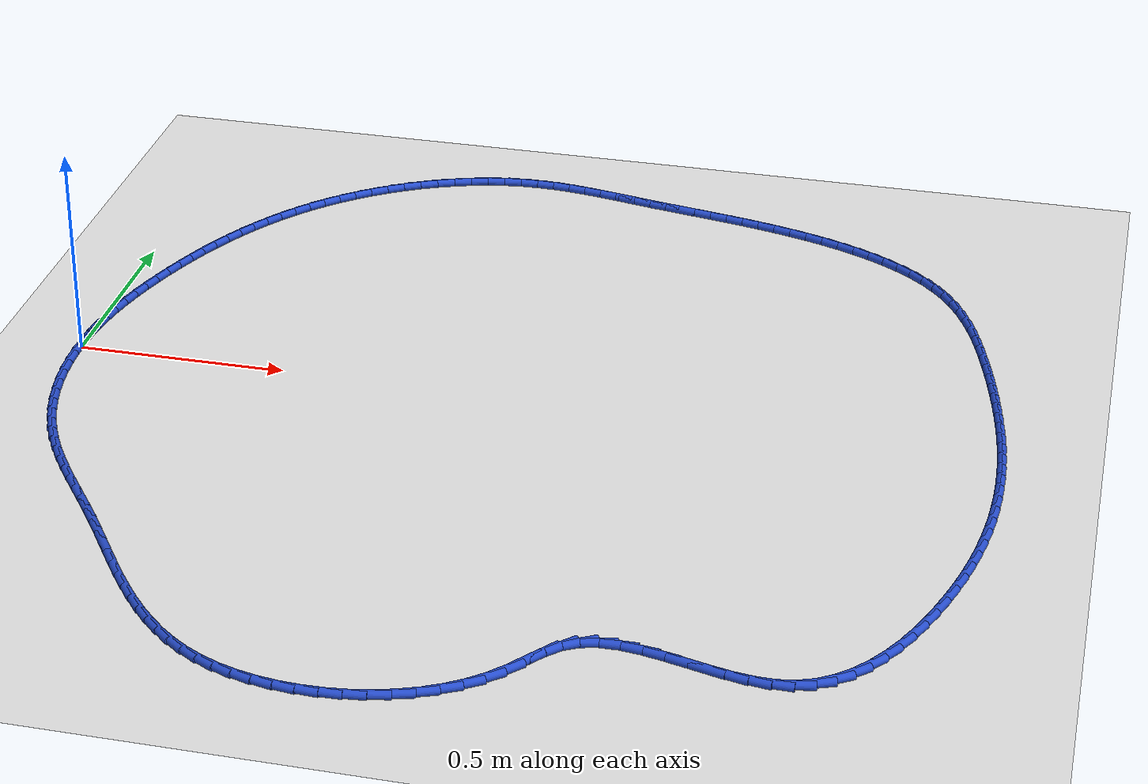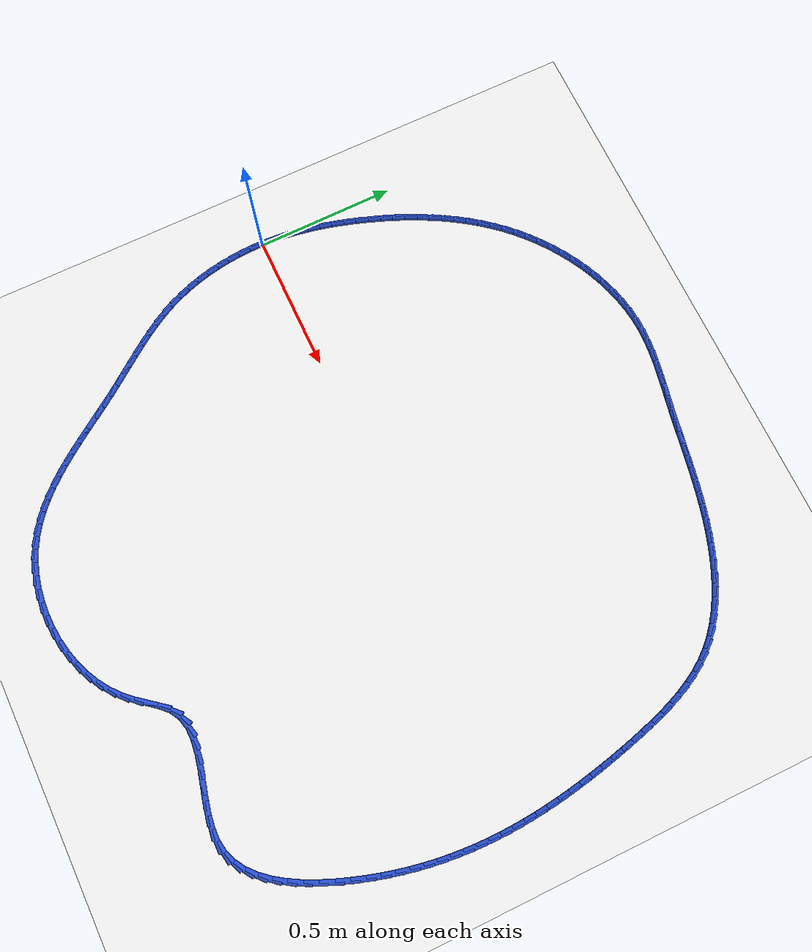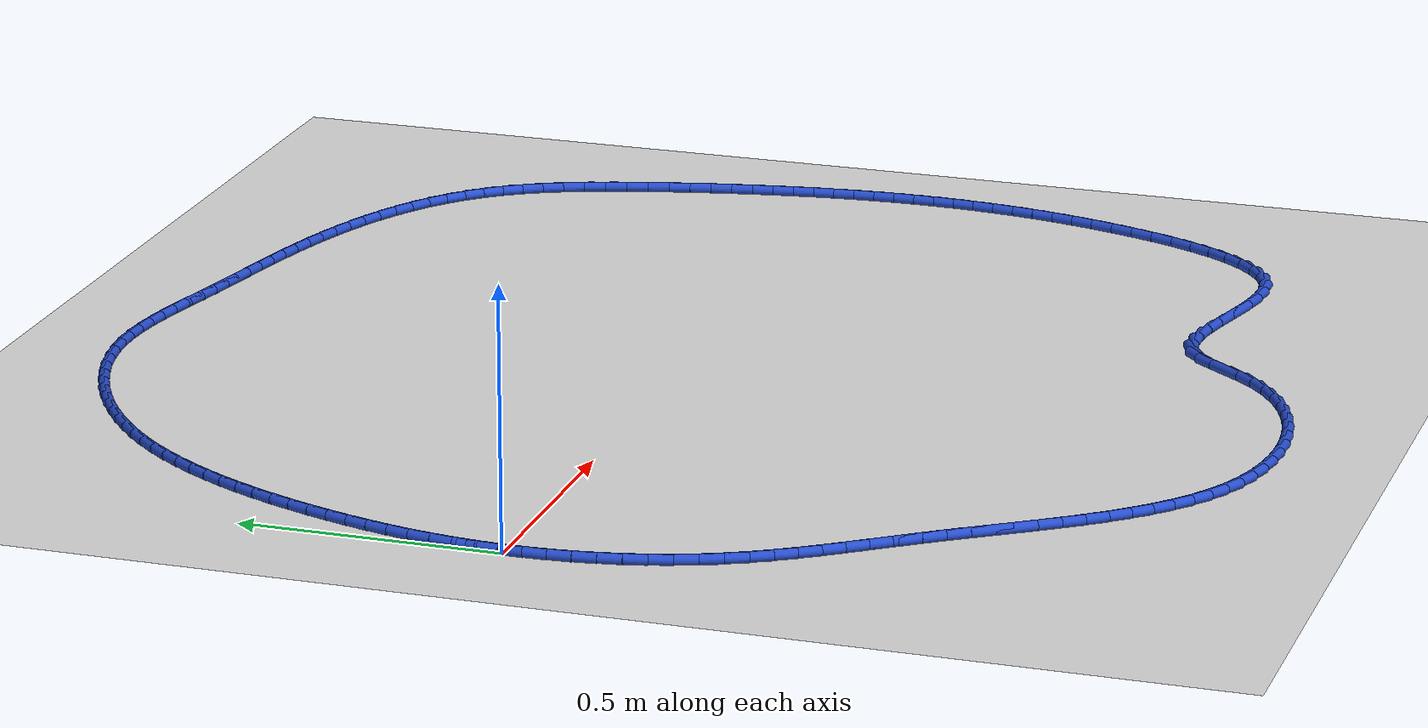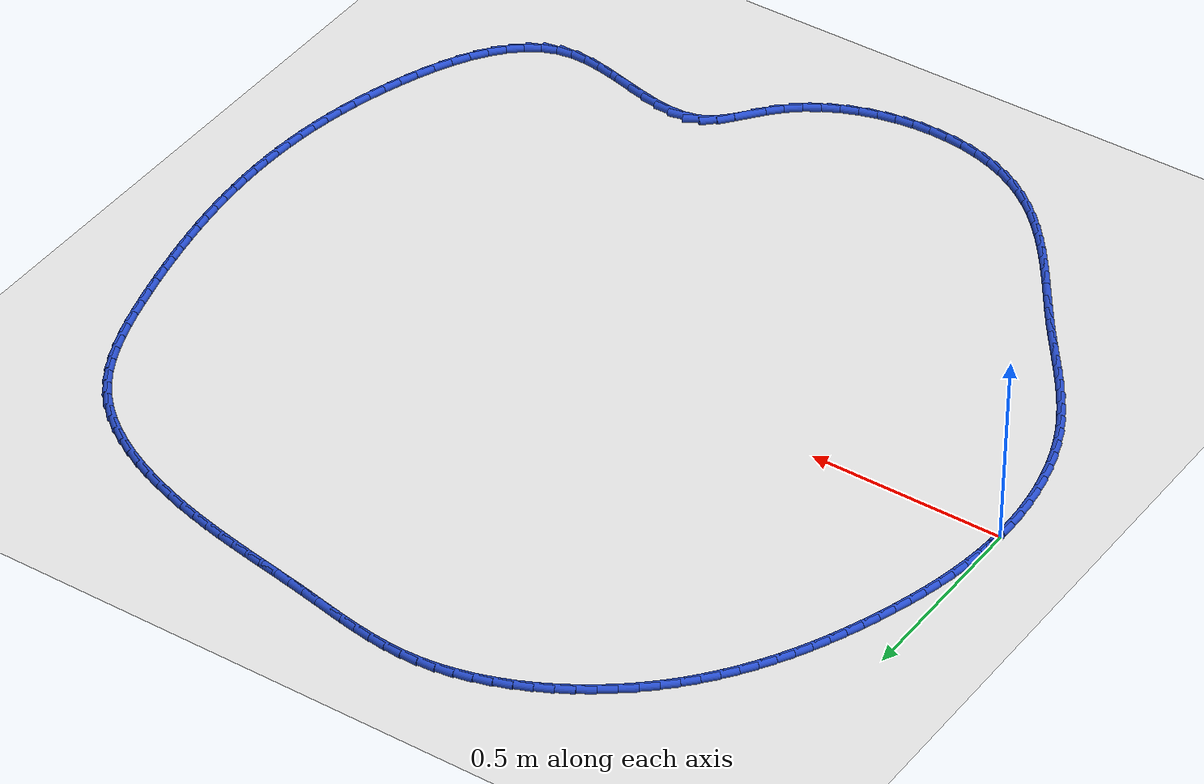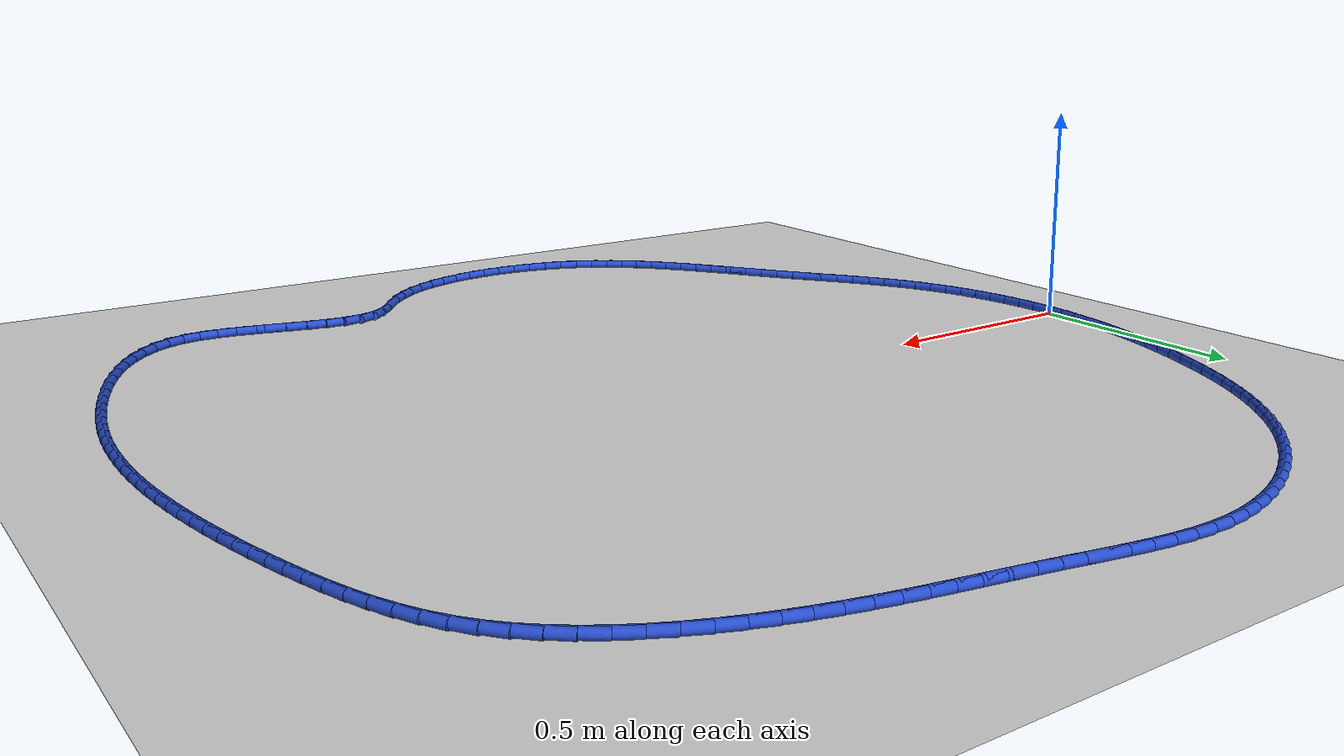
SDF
<sdf version="1.6">
 <world name="default">
  <light name="sun" type="directional">
   <pose>0 0 10 0 -0 0</pose>
   <diffuse>0.8 0.8 0.8 1</diffuse>
   <specular>0.2 0.2 0.2 1</specular>
   <attenuation>
    <range>1000</range>
    <constant>0.9</constant>
    <linear>0.01</linear>
    <quadratic>0.001</quadratic>
   </attenuation>
   <direction>-0.5 0.1 -0.9</direction>
  </light>
  <model name="ground_plane">
   <static>1</static>
   <link name="link">
    <collision name="collision">
     <geometry><plane><normal>0 0 1</normal><size>100 100</size></plane></geometry>
     <surface><friction><ode><mu>100</mu><mu2>50</mu2></ode></friction></surface>
    </collision>
    <visual name="visual">
     <cast_shadows>0</cast_shadows>
     <geometry><plane><normal>0 0 1</normal><size>100 100</size></plane></geometry>
     <material>
      <script><uri>file://media/materials/scripts/gazebo.material</uri><name>Gazebo/WhiteGlow</name></script>
     </material>
    </visual>
   </link>
  </model>
  <gravity>0 0 -9.8</gravity>
  <magnetic_field>6e-06 2.3e-05 -4.2e-05</magnetic_field>
  <atmosphere type="adiabatic"/>
  <physics name="default_physics" default="0" type="ode">
   <max_step_size>0.001</max_step_size>
   <real_time_factor>1</real_time_factor>
   <real_time_update_rate>1000</real_time_update_rate>
  </physics>
  <scene><ambient>0.4 0.4 0.4 1</ambient><background>0.7 0.7 0.7 1</background><shadows>1</shadows></scene>
  <spherical_coordinates>
   <surface_model>EARTH_WGS84</surface_model>
   <latitude_deg>0</latitude_deg>
   <longitude_deg>0</longitude_deg>
   <elevation>0</elevation>
   <heading_deg>0</heading_deg>
  </spherical_coordinates>
  <model name="line">
   <link name="link_0">
    <pose>5.0306980803327406e-17 1.3877787807814457e-17 0.01 0 1.57 1.5260147244363123</pose>
    <collision name="collision">
     <geometry><cylinder><radius>0.01</radius><length>0.08</length></cylinder></geometry>
    </collision>
    <visual name="visual">
     <material>
      <script><name>Gazebo/Blue</name><uri>file://media/materials/scripts/gazebo.material</uri></script>
     </material>
     <geometry><cylinder><radius>0.01</radius><length>0.08</length></cylinder></geometry>
    </visual>
   </link>
   <link name="link_1">
    <pose>0.0019904885369562845 0.0444190847222737 0.01 0 1.57 1.4812232621702883</pose>
    <collision name="collision">
     <geometry><cylinder><radius>0.01</radius><length>0.08</length></cylinder></geometry>
    </collision>
    <visual name="visual">
     <material>
      <script><name>Gazebo/Blue</name><uri>file://media/materials/scripts/gazebo.material</uri></script>
     </material>
     <geometry><cylinder><radius>0.01</radius><length>0.08</length></cylinder></geometry>
    </visual>
   </link>
   <link name="link_2">
    <pose>0.005955106309354074 0.08856191898155275 0.01 0 1.57 1.439000569083363</pose>
    <collision name="collision">
     <geometry><cylinder><radius>0.01</radius><length>0.08</length></cylinder></geometry>
    </collision>
    <visual name="visual">
     <material>
      <script><name>Gazebo/Blue</name><uri>file://media/materials/scripts/gazebo.material</uri></script>
     </material>
     <geometry><cylinder><radius>0.01</radius><length>0.08</length></cylinder></geometry>
    </visual>
   </link>
   <link name="link_3">
    <pose>0.011770059089839587 0.13242710110053268 0.01 0 1.57 1.3994675310852336</pose>
    <collision name="collision">
     <geometry><cylinder><radius>0.01</radius><length>0.08</length></cylinder></geometry>
    </collision>
    <visual name="visual">
     <material>
      <script><name>Gazebo/Blue</name><uri>file://media/materials/scripts/gazebo.material</uri></script>
     </material>
     <geometry><cylinder><radius>0.01</radius><length>0.08</length></cylinder></geometry>
    </visual>
   </link>
   <link name="link_4">
    <pose>0.01931155265105896 0.17601322940190903 0.01 0 1.57 1.362697493794268</pose>
    <collision name="collision">
     <geometry><cylinder><radius>0.01</radius><length>0.08</length></cylinder></geometry>
    </collision>
    <visual name="visual">
     <material>
      <script><name>Gazebo/Blue</name><uri>file://media/materials/scripts/gazebo.material</uri></script>
     </material>
     <geometry><cylinder><radius>0.01</radius><length>0.08</length></cylinder></geometry>
    </visual>
   </link>
   <link name="link_5">
    <pose>0.028455792765658367 0.2193189022083774 0.01 0 1.57 1.3287240169238606</pose>
    <collision name="collision">
     <geometry><cylinder><radius>0.01</radius><length>0.08</length></cylinder></geometry>
    </collision>
    <visual name="visual">
     <material>
      <script><name>Gazebo/Blue</name><uri>file://media/materials/scripts/gazebo.material</uri></script>
     </material>
     <geometry><cylinder><radius>0.01</radius><length>0.08</length></cylinder></geometry>
    </visual>
   </link>
   <link name="link_6">
    <pose>0.03907898520628396 0.26234271784263336 0.01 0 1.57 1.2975490997938268</pose>
    <collision name="collision">
     <geometry><cylinder><radius>0.01</radius><length>0.08</length></cylinder></geometry>
    </collision>
    <visual name="visual">
     <material>
      <script><name>Gazebo/Blue</name><uri>file://media/materials/scripts/gazebo.material</uri></script>
     </material>
     <geometry><cylinder><radius>0.01</radius><length>0.08</length></cylinder></geometry>
    </visual>
   </link>
   <link name="link_7">
    <pose>0.0510573357455819 0.30508327462737245 0.01 0 1.57 1.2691512236758864</pose>
    <collision name="collision">
     <geometry><cylinder><radius>0.01</radius><length>0.08</length></cylinder></geometry>
    </collision>
    <visual name="visual">
     <material>
      <script><name>Gazebo/Blue</name><uri>file://media/materials/scripts/gazebo.material</uri></script>
     </material>
     <geometry><cylinder><radius>0.01</radius><length>0.08</length></cylinder></geometry>
    </visual>
   </link>
   <link name="link_8">
    <pose>0.06426705015619832 0.34753917088529 0.01 0 1.57 1.2434890691378662</pose>
    <collision name="collision">
     <geometry><cylinder><radius>0.01</radius><length>0.08</length></cylinder></geometry>
    </collision>
    <visual name="visual">
     <material>
      <script><name>Gazebo/Blue</name><uri>file://media/materials/scripts/gazebo.material</uri></script>
     </material>
     <geometry><cylinder><radius>0.01</radius><length>0.08</length></cylinder></geometry>
    </visual>
   </link>
   <link name="link_9">
    <pose>0.07858448455763797 0.38970893372503573 0.01 0 1.57 1.2192639421745357</pose>
    <collision name="collision">
     <geometry><cylinder><radius>0.01</radius><length>0.08</length></cylinder></geometry>
    </collision>
    <visual name="visual">
     <material>
      <script><name>Gazebo/Blue</name><uri>file://media/materials/scripts/gazebo.material</uri></script>
     </material>
     <geometry><cylinder><radius>0.01</radius><length>0.08</length></cylinder></geometry>
    </visual>
   </link>
   <link name="link_10">
    <pose>0.09393663902727978 0.4315671019845059 0.01 0 1.57 1.1933516240119146</pose>
    <collision name="collision">
     <geometry><cylinder><radius>0.01</radius><length>0.08</length></cylinder></geometry>
    </collision>
    <visual name="visual">
     <material>
      <script><name>Gazebo/Blue</name><uri>file://media/materials/scripts/gazebo.material</uri></script>
     </material>
     <geometry><cylinder><radius>0.01</radius><length>0.08</length></cylinder></geometry>
    </visual>
   </link>
   <link name="link_11">
    <pose>0.11037451438381249 0.4730294796893706 0.01 0 1.57 1.1652217401002263</pose>
    <collision name="collision">
     <geometry><cylinder><radius>0.01</radius><length>0.08</length></cylinder></geometry>
    </collision>
    <visual name="visual">
     <material>
      <script><name>Gazebo/Blue</name><uri>file://media/materials/scripts/gazebo.material</uri></script>
     </material>
     <geometry><cylinder><radius>0.01</radius><length>0.08</length></cylinder></geometry>
    </visual>
   </link>
   <link name="link_12">
    <pose>0.12796773982584467 0.5140030472535612 0.01 0 1.57 1.134805137264003</pose>
    <collision name="collision">
     <geometry><cylinder><radius>0.01</radius><length>0.08</length></cylinder></geometry>
    </collision>
    <visual name="visual">
     <material>
      <script><name>Gazebo/Blue</name><uri>file://media/materials/scripts/gazebo.material</uri></script>
     </material>
     <geometry><cylinder><radius>0.01</radius><length>0.08</length></cylinder></geometry>
    </visual>
   </link>
   <link name="link_13">
    <pose>0.1467859445519847 0.5543947850910084 0.01 0 1.57 1.1020382116200267</pose>
    <collision name="collision">
     <geometry><cylinder><radius>0.01</radius><length>0.08</length></cylinder></geometry>
    </collision>
    <visual name="visual">
     <material>
      <script><name>Gazebo/Blue</name><uri>file://media/materials/scripts/gazebo.material</uri></script>
     </material>
     <geometry><cylinder><radius>0.01</radius><length>0.08</length></cylinder></geometry>
    </visual>
   </link>
   <link name="link_14">
    <pose>0.16689875776084134 0.5941116736156439 0.01 0 1.57 1.0668678408947943</pose>
    <collision name="collision">
     <geometry><cylinder><radius>0.01</radius><length>0.08</length></cylinder></geometry>
    </collision>
    <visual name="visual">
     <material>
      <script><name>Gazebo/Blue</name><uri>file://media/materials/scripts/gazebo.material</uri></script>
     </material>
     <geometry><cylinder><radius>0.01</radius><length>0.08</length></cylinder></geometry>
    </visual>
   </link>
   <link name="link_15">
    <pose>0.18837580865102302 0.6330606932413984 0.01 0 1.57 1.029257130996938</pose>
    <collision name="collision">
     <geometry><cylinder><radius>0.01</radius><length>0.08</length></cylinder></geometry>
    </collision>
    <visual name="visual">
     <material>
      <script><name>Gazebo/Blue</name><uri>file://media/materials/scripts/gazebo.material</uri></script>
     </material>
     <geometry><cylinder><radius>0.01</radius><length>0.08</length></cylinder></geometry>
    </visual>
   </link>
   <link name="link_16">
    <pose>0.21128672642113833 0.6711488243822031 0.01 0 1.57 0.98919190727379</pose>
    <collision name="collision">
     <geometry><cylinder><radius>0.01</radius><length>0.08</length></cylinder></geometry>
    </collision>
    <visual name="visual">
     <material>
      <script><name>Gazebo/Blue</name><uri>file://media/materials/scripts/gazebo.material</uri></script>
     </material>
     <geometry><cylinder><radius>0.01</radius><length>0.08</length></cylinder></geometry>
    </visual>
   </link>
   <link name="link_17">
    <pose>0.23570114026979583 0.7082830474519894 0.01 0 1.57 0.9466877524308595</pose>
    <collision name="collision">
     <geometry><cylinder><radius>0.01</radius><length>0.08</length></cylinder></geometry>
    </collision>
    <visual name="visual">
     <material>
      <script><name>Gazebo/Blue</name><uri>file://media/materials/scripts/gazebo.material</uri></script>
     </material>
     <geometry><cylinder><radius>0.01</radius><length>0.08</length></cylinder></geometry>
    </visual>
   </link>
   <link name="link_18">
    <pose>0.261688679395604 0.7443703428646884 0.01 0 1.57 0.9017972293461288</pose>
    <collision name="collision">
     <geometry><cylinder><radius>0.01</radius><length>0.08</length></cylinder></geometry>
    </collision>
    <visual name="visual">
     <material>
      <script><name>Gazebo/Blue</name><uri>file://media/materials/scripts/gazebo.material</uri></script>
     </material>
     <geometry><cylinder><radius>0.01</radius><length>0.08</length></cylinder></geometry>
    </visual>
   </link>
   <link name="link_19">
    <pose>0.28931897299717135 0.779317691034231 0.01 0 1.57 0.8546167411335518</pose>
    <collision name="collision">
     <geometry><cylinder><radius>0.01</radius><length>0.08</length></cylinder></geometry>
    </collision>
    <visual name="visual">
     <material>
      <script><name>Gazebo/Blue</name><uri>file://media/materials/scripts/gazebo.material</uri></script>
     </material>
     <geometry><cylinder><radius>0.01</radius><length>0.08</length></cylinder></geometry>
    </visual>
   </link>
   <link name="link_20">
    <pose>0.3186616502731066 0.8130320723745486 0.01 0 1.57 0.8052923010427596</pose>
    <collision name="collision">
     <geometry><cylinder><radius>0.01</radius><length>0.08</length></cylinder></geometry>
    </collision>
    <visual name="visual">
     <material>
      <script><name>Gazebo/Blue</name><uri>file://media/materials/scripts/gazebo.material</uri></script>
     </material>
     <geometry><cylinder><radius>0.01</radius><length>0.08</length></cylinder></geometry>
    </visual>
   </link>
   <link name="link_21">
    <pose>0.34978634042201817 0.8454204672995723 0.01 0 1.57 0.7541902982342445</pose>
    <collision name="collision">
     <geometry><cylinder><radius>0.01</radius><length>0.08</length></cylinder></geometry>
    </collision>
    <visual name="visual">
     <material>
      <script><name>Gazebo/Blue</name><uri>file://media/materials/scripts/gazebo.material</uri></script>
     </material>
     <geometry><cylinder><radius>0.01</radius><length>0.08</length></cylinder></geometry>
    </visual>
   </link>
   <link name="link_22">
    <pose>0.3827466531985884 0.8763851689411416 0.01 0 1.57 0.7027724105210611</pose>
    <collision name="collision">
     <geometry><cylinder><radius>0.01</radius><length>0.08</length></cylinder></geometry>
    </collision>
    <visual name="visual">
     <material>
      <script><name>Gazebo/Blue</name><uri>file://media/materials/scripts/gazebo.material</uri></script>
     </material>
     <geometry><cylinder><radius>0.01</radius><length>0.08</length></cylinder></geometry>
    </visual>
   </link>
   <link name="link_23">
    <pose>0.4174598176858261 0.9057885655078715 0.01 0 1.57 0.6513601458947901</pose>
    <collision name="collision">
     <geometry><cylinder><radius>0.01</radius><length>0.08</length></cylinder></geometry>
    </collision>
    <visual name="visual">
     <material>
      <script><name>Gazebo/Blue</name><uri>file://media/materials/scripts/gazebo.material</uri></script>
     </material>
     <geometry><cylinder><radius>0.01</radius><length>0.08</length></cylinder></geometry>
    </visual>
   </link>
   <link name="link_24">
    <pose>0.4537741127236348 0.9334728703982391 0.01 0 1.57 0.5994964725189268</pose>
    <collision name="collision">
     <geometry><cylinder><radius>0.01</radius><length>0.08</length></cylinder></geometry>
    </collision>
    <visual name="visual">
     <material>
      <script><name>Gazebo/Blue</name><uri>file://media/materials/scripts/gazebo.material</uri></script>
     </material>
     <geometry><cylinder><radius>0.01</radius><length>0.08</length></cylinder></geometry>
    </visual>
   </link>
   <link name="link_25">
    <pose>0.49153728418290193 0.959280141064228 0.01 0 1.57 0.5467284496184864</pose>
    <collision name="collision">
     <geometry><cylinder><radius>0.01</radius><length>0.08</length></cylinder></geometry>
    </collision>
    <visual name="visual">
     <material>
      <script><name>Gazebo/Blue</name><uri>file://media/materials/scripts/gazebo.material</uri></script>
     </material>
     <geometry><cylinder><radius>0.01</radius><length>0.08</length></cylinder></geometry>
    </visual>
   </link>
   <link name="link_26">
    <pose>0.5305970779345149 0.9830524349578204 0.01 0 1.57 0.49260954397146894</pose>
    <collision name="collision">
     <geometry><cylinder><radius>0.01</radius><length>0.08</length></cylinder></geometry>
    </collision>
    <visual name="visual">
     <material>
      <script><name>Gazebo/Blue</name><uri>file://media/materials/scripts/gazebo.material</uri></script>
     </material>
     <geometry><cylinder><radius>0.01</radius><length>0.08</length></cylinder></geometry>
    </visual>
   </link>
   <link name="link_27">
    <pose>0.5708012398493613 1.004631809531 0.01 0 1.57 0.4366985960987318</pose>
    <collision name="collision">
     <geometry><cylinder><radius>0.01</radius><length>0.08</length></cylinder></geometry>
    </collision>
    <visual name="visual">
     <material>
      <script><name>Gazebo/Blue</name><uri>file://media/materials/scripts/gazebo.material</uri></script>
     </material>
     <geometry><cylinder><radius>0.01</radius><length>0.08</length></cylinder></geometry>
    </visual>
   </link>
   <link name="link_28">
    <pose>0.6119975157983282 1.0238603222357496 0.01 0 1.57 0.3785618344518044</pose>
    <collision name="collision">
     <geometry><cylinder><radius>0.01</radius><length>0.08</length></cylinder></geometry>
    </collision>
    <visual name="visual">
     <material>
      <script><name>Gazebo/Blue</name><uri>file://media/materials/scripts/gazebo.material</uri></script>
     </material>
     <geometry><cylinder><radius>0.01</radius><length>0.08</length></cylinder></geometry>
    </visual>
   </link>
   <link name="link_29">
    <pose>0.6540336516523026 1.0405800305240513 0.01 0 1.57 0.3177789747133592</pose>
    <collision name="collision">
     <geometry><cylinder><radius>0.01</radius><length>0.08</length></cylinder></geometry>
    </collision>
    <visual name="visual">
     <material>
      <script><name>Gazebo/Blue</name><uri>file://media/materials/scripts/gazebo.material</uri></script>
     </material>
     <geometry><cylinder><radius>0.01</radius><length>0.08</length></cylinder></geometry>
    </visual>
   </link>
   <link name="link_30">
    <pose>0.6967573932821725 1.054632991847889 0.01 0 1.57 0.2539546093797289</pose>
    <collision name="collision">
     <geometry><cylinder><radius>0.01</radius><length>0.08</length></cylinder></geometry>
    </collision>
    <visual name="visual">
     <material>
      <script><name>Gazebo/Blue</name><uri>file://media/materials/scripts/gazebo.material</uri></script>
     </material>
     <geometry><cylinder><radius>0.01</radius><length>0.08</length></cylinder></geometry>
    </visual>
   </link>
   <link name="link_31">
    <pose>0.7400164865588247 1.0658612636592453 0.01 0 1.57 0.18673611924459146</pose>
    <collision name="collision">
     <geometry><cylinder><radius>0.01</radius><length>0.08</length></cylinder></geometry>
    </collision>
    <visual name="visual">
     <material>
      <script><name>Gazebo/Blue</name><uri>file://media/materials/scripts/gazebo.material</uri></script>
     </material>
     <geometry><cylinder><radius>0.01</radius><length>0.08</length></cylinder></geometry>
    </visual>
   </link>
   <link name="link_32">
    <pose>0.7836586773531469 1.0741069034101027 0.01 0 1.57 0.11583904248746658</pose>
    <collision name="collision">
     <geometry><cylinder><radius>0.01</radius><length>0.08</length></cylinder></geometry>
    </collision>
    <visual name="visual">
     <material>
      <script><name>Gazebo/Blue</name><uri>file://media/materials/scripts/gazebo.material</uri></script>
     </material>
     <geometry><cylinder><radius>0.01</radius><length>0.08</length></cylinder></geometry>
    </visual>
   </link>
   <link name="link_33">
    <pose>0.8275317115360259 1.0792119685524442 0.01 0 1.57 0.0412070935962064</pose>
    <collision name="collision">
     <geometry><cylinder><radius>0.01</radius><length>0.08</length></cylinder></geometry>
    </collision>
    <visual name="visual">
     <material>
      <script><name>Gazebo/Blue</name><uri>file://media/materials/scripts/gazebo.material</uri></script>
     </material>
     <geometry><cylinder><radius>0.01</radius><length>0.08</length></cylinder></geometry>
    </visual>
   </link>
   <link name="link_34">
    <pose>0.8714844123988754 1.081024157440585 0.01 0 1.57 -0.030846933155782144</pose>
    <collision name="collision">
     <geometry><cylinder><radius>0.01</radius><length>0.08</length></cylinder></geometry>
    </collision>
    <visual name="visual">
     <material>
      <script><name>Gazebo/Blue</name><uri>file://media/materials/scripts/gazebo.material</uri></script>
     </material>
     <geometry><cylinder><radius>0.01</radius><length>0.08</length></cylinder></geometry>
    </visual>
   </link>
   <link name="link_35">
    <pose>0.9154185726897079 1.0796684933210483 0.01 0 1.57 -0.09089073254683624</pose>
    <collision name="collision">
     <geometry><cylinder><radius>0.01</radius><length>0.08</length></cylinder></geometry>
    </collision>
    <visual name="visual">
     <material>
      <script><name>Gazebo/Blue</name><uri>file://media/materials/scripts/gazebo.material</uri></script>
     </material>
     <geometry><cylinder><radius>0.01</radius><length>0.08</length></cylinder></geometry>
    </visual>
   </link>
   <link name="link_36">
    <pose>0.9593119972415886 1.0756679654503467 0.01 0 1.57 -0.13807893030556345</pose>
    <collision name="collision">
     <geometry><cylinder><radius>0.01</radius><length>0.08</length></cylinder></geometry>
    </collision>
    <visual name="visual">
     <material>
      <script><name>Gazebo/Blue</name><uri>file://media/materials/scripts/gazebo.material</uri></script>
     </material>
     <geometry><cylinder><radius>0.01</radius><length>0.08</length></cylinder></geometry>
    </visual>
   </link>
   <link name="link_37">
    <pose>1.0031483661213207 1.069576323237492 0.01 0 1.57 -0.1725911667560794</pose>
    <collision name="collision">
     <geometry><cylinder><radius>0.01</radius><length>0.08</length></cylinder></geometry>
    </collision>
    <visual name="visual">
     <material>
      <script><name>Gazebo/Blue</name><uri>file://media/materials/scripts/gazebo.material</uri></script>
     </material>
     <geometry><cylinder><radius>0.01</radius><length>0.08</length></cylinder></geometry>
    </visual>
   </link>
   <link name="link_38">
    <pose>1.0469113593957065 1.0619473160914963 0.01 0 1.57 -0.1947072820093124</pose>
    <collision name="collision">
     <geometry><cylinder><radius>0.01</radius><length>0.08</length></cylinder></geometry>
    </collision>
    <visual name="visual">
     <material>
      <script><name>Gazebo/Blue</name><uri>file://media/materials/scripts/gazebo.material</uri></script>
     </material>
     <geometry><cylinder><radius>0.01</radius><length>0.08</length></cylinder></geometry>
    </visual>
   </link>
   <link name="link_39">
    <pose>1.0905846571315483 1.0533346934213708 0.01 0 1.57 -0.20464670937285362</pose>
    <collision name="collision">
     <geometry><cylinder><radius>0.01</radius><length>0.08</length></cylinder></geometry>
    </collision>
    <visual name="visual">
     <material>
      <script><name>Gazebo/Blue</name><uri>file://media/materials/scripts/gazebo.material</uri></script>
     </material>
     <geometry><cylinder><radius>0.01</radius><length>0.08</length></cylinder></geometry>
    </visual>
   </link>
   <link name="link_40">
    <pose>1.1341519393956485 1.0442922046361267 0.01 0 1.57 -0.202477934255128</pose>
    <collision name="collision">
     <geometry><cylinder><radius>0.01</radius><length>0.08</length></cylinder></geometry>
    </collision>
    <visual name="visual">
     <material>
      <script><name>Gazebo/Blue</name><uri>file://media/materials/scripts/gazebo.material</uri></script>
     </material>
     <geometry><cylinder><radius>0.01</radius><length>0.08</length></cylinder></geometry>
    </visual>
   </link>
   <link name="link_41">
    <pose>1.177596903277948 1.035373340506603 0.01 0 1.57 -0.19210740276732197</pose>
    <collision name="collision">
     <geometry><cylinder><radius>0.01</radius><length>0.08</length></cylinder></geometry>
    </collision>
    <visual name="visual">
     <material>
      <script><name>Gazebo/Blue</name><uri>file://media/materials/scripts/gazebo.material</uri></script>
     </material>
     <geometry><cylinder><radius>0.01</radius><length>0.08</length></cylinder></geometry>
    </visual>
   </link>
   <link name="link_42">
    <pose>1.2209153533538637 1.0269476387652823 0.01 0 1.57 -0.18458665404068675</pose>
    <collision name="collision">
     <geometry><cylinder><radius>0.01</radius><length>0.08</length></cylinder></geometry>
    </collision>
    <visual name="visual">
     <material>
      <script><name>Gazebo/Blue</name><uri>file://media/materials/scripts/gazebo.material</uri></script>
     </material>
     <geometry><cylinder><radius>0.01</radius><length>0.08</length></cylinder></geometry>
    </visual>
   </link>
   <link name="link_43">
    <pose>1.2641364574825134 1.0188777377213005 0.01 0 1.57 -0.18189383639944168</pose>
    <collision name="collision">
     <geometry><cylinder><radius>0.01</radius><length>0.08</length></cylinder></geometry>
    </collision>
    <visual name="visual">
     <material>
      <script><name>Gazebo/Blue</name><uri>file://media/materials/scripts/gazebo.material</uri></script>
     </material>
     <geometry><cylinder><radius>0.01</radius><length>0.08</length></cylinder></geometry>
    </visual>
   </link>
   <link name="link_44">
    <pose>1.3072950809854798 1.0109397122488666 0.01 0 1.57 -0.184071219256805</pose>
    <collision name="collision">
     <geometry><cylinder><radius>0.01</radius><length>0.08</length></cylinder></geometry>
    </collision>
    <visual name="visual">
     <material>
      <script><name>Gazebo/Blue</name><uri>file://media/materials/scripts/gazebo.material</uri></script>
     </material>
     <geometry><cylinder><radius>0.01</radius><length>0.08</length></cylinder></geometry>
    </visual>
   </link>
   <link name="link_45">
    <pose>1.3504260891843447 1.0029096372221902 0.01 0 1.57 -0.19111093273985194</pose>
    <collision name="collision">
     <geometry><cylinder><radius>0.01</radius><length>0.08</length></cylinder></geometry>
    </collision>
    <visual name="visual">
     <material>
      <script><name>Gazebo/Blue</name><uri>file://media/materials/scripts/gazebo.material</uri></script>
     </material>
     <geometry><cylinder><radius>0.01</radius><length>0.08</length></cylinder></geometry>
    </visual>
   </link>
   <link name="link_46">
    <pose>1.3935643474006902 0.9945635875154802 0.01 0 1.57 -0.202953517383078</pose>
    <collision name="collision">
     <geometry><cylinder><radius>0.01</radius><length>0.08</length></cylinder></geometry>
    </collision>
    <visual name="visual">
     <material>
      <script><name>Gazebo/Blue</name><uri>file://media/materials/scripts/gazebo.material</uri></script>
     </material>
     <geometry><cylinder><radius>0.01</radius><length>0.08</length></cylinder></geometry>
    </visual>
   </link>
   <link name="link_47">
    <pose>1.4367447209560988 0.9856776380029463 0.01 0 1.57 -0.2194845324050165</pose>
    <collision name="collision">
     <geometry><cylinder><radius>0.01</radius><length>0.08</length></cylinder></geometry>
    </collision>
    <visual name="visual">
     <material>
      <script><name>Gazebo/Blue</name><uri>file://media/materials/scripts/gazebo.material</uri></script>
     </material>
     <geometry><cylinder><radius>0.01</radius><length>0.08</length></cylinder></geometry>
    </visual>
   </link>
   <link name="link_48">
    <pose>1.4800020751721525 0.9760278635587967 0.01 0 1.57 -0.2405298143651853</pose>
    <collision name="collision">
     <geometry><cylinder><radius>0.01</radius><length>0.08</length></cylinder></geometry>
    </collision>
    <visual name="visual">
     <material>
      <script><name>Gazebo/Blue</name><uri>file://media/materials/scripts/gazebo.material</uri></script>
     </material>
     <geometry><cylinder><radius>0.01</radius><length>0.08</length></cylinder></geometry>
    </visual>
   </link>
   <link name="link_49">
    <pose>1.5233712753704336 0.9653903390572418 0.01 0 1.57 -0.2658501743627113</pose>
    <collision name="collision">
     <geometry><cylinder><radius>0.01</radius><length>0.08</length></cylinder></geometry>
    </collision>
    <visual name="visual">
     <material>
      <script><name>Gazebo/Blue</name><uri>file://media/materials/scripts/gazebo.material</uri></script>
     </material>
     <geometry><cylinder><radius>0.01</radius><length>0.08</length></cylinder></geometry>
    </visual>
   </link>
   <link name="link_50">
    <pose>1.5668863192249292 0.9535413860957317 0.01 0 1.57 -0.29518545745611224</pose>
    <collision name="collision">
     <geometry><cylinder><radius>0.01</radius><length>0.08</length></cylinder></geometry>
    </collision>
    <visual name="visual">
     <material>
      <script><name>Gazebo/Blue</name><uri>file://media/materials/scripts/gazebo.material</uri></script>
     </material>
     <geometry><cylinder><radius>0.01</radius><length>0.08</length></cylinder></geometry>
    </visual>
   </link>
   <link name="link_51">
    <pose>1.6104699896521077 0.9402889511683342 0.01 0 1.57 -0.32866140924841397</pose>
    <collision name="collision">
     <geometry><cylinder><radius>0.01</radius><length>0.08</length></cylinder></geometry>
    </collision>
    <visual name="visual">
     <material>
      <script><name>Gazebo/Blue</name><uri>file://media/materials/scripts/gazebo.material</uri></script>
     </material>
     <geometry><cylinder><radius>0.01</radius><length>0.08</length></cylinder></geometry>
    </visual>
   </link>
   <link name="link_52">
    <pose>1.6538256396673474 0.9255033775956852 0.01 0 1.57 -0.3667156572551275</pose>
    <collision name="collision">
     <geometry><cylinder><radius>0.01</radius><length>0.08</length></cylinder></geometry>
    </collision>
    <visual name="visual">
     <material>
      <script><name>Gazebo/Blue</name><uri>file://media/materials/scripts/gazebo.material</uri></script>
     </material>
     <geometry><cylinder><radius>0.01</radius><length>0.08</length></cylinder></geometry>
    </visual>
   </link>
   <link name="link_53">
    <pose>1.6966309251855796 0.9090623158954425 0.01 0 1.57 -0.40987348086256875</pose>
    <collision name="collision">
     <geometry><cylinder><radius>0.01</radius><length>0.08</length></cylinder></geometry>
    </collision>
    <visual name="visual">
     <material>
      <script><name>Gazebo/Blue</name><uri>file://media/materials/scripts/gazebo.material</uri></script>
     </material>
     <geometry><cylinder><radius>0.01</radius><length>0.08</length></cylinder></geometry>
    </visual>
   </link>
   <link name="link_54">
    <pose>1.7385635021217336 0.8908434165852644 0.01 0 1.57 -0.4587324882292901</pose>
    <collision name="collision">
     <geometry><cylinder><radius>0.01</radius><length>0.08</length></cylinder></geometry>
    </collision>
    <visual name="visual">
     <material>
      <script><name>Gazebo/Blue</name><uri>file://media/materials/scripts/gazebo.material</uri></script>
     </material>
     <geometry><cylinder><radius>0.01</radius><length>0.08</length></cylinder></geometry>
    </visual>
   </link>
   <link name="link_55">
    <pose>1.77930102639074 0.8707243301828093 0.01 0 1.57 -0.5139434324421377</pose>
    <collision name="collision">
     <geometry><cylinder><radius>0.01</radius><length>0.08</length></cylinder></geometry>
    </collision>
    <visual name="visual">
     <material>
      <script><name>Gazebo/Blue</name><uri>file://media/materials/scripts/gazebo.material</uri></script>
     </material>
     <geometry><cylinder><radius>0.01</radius><length>0.08</length></cylinder></geometry>
    </visual>
   </link>
   <link name="link_56">
    <pose>1.8185211539075303 0.8485827072057349 0.01 0 1.57 -0.57617317073375</pose>
    <collision name="collision">
     <geometry><cylinder><radius>0.01</radius><length>0.08</length></cylinder></geometry>
    </collision>
    <visual name="visual">
     <material>
      <script><name>Gazebo/Blue</name><uri>file://media/materials/scripts/gazebo.material</uri></script>
     </material>
     <geometry><cylinder><radius>0.01</radius><length>0.08</length></cylinder></geometry>
    </visual>
   </link>
   <link name="link_57">
    <pose>1.8559015405870343 0.8242961981717001 0.01 0 1.57 -0.6460407203655865</pose>
    <collision name="collision">
     <geometry><cylinder><radius>0.01</radius><length>0.08</length></cylinder></geometry>
    </collision>
    <visual name="visual">
     <material>
      <script><name>Gazebo/Blue</name><uri>file://media/materials/scripts/gazebo.material</uri></script>
     </material>
     <geometry><cylinder><radius>0.01</radius><length>0.08</length></cylinder></geometry>
    </visual>
   </link>
   <link name="link_58">
    <pose>1.8911198423441828 0.7977424535983626 0.01 0 1.57 -0.7240175976298837</pose>
    <collision name="collision">
     <geometry><cylinder><radius>0.01</radius><length>0.08</length></cylinder></geometry>
    </collision>
    <visual name="visual">
     <material>
      <script><name>Gazebo/Blue</name><uri>file://media/materials/scripts/gazebo.material</uri></script>
     </material>
     <geometry><cylinder><radius>0.01</radius><length>0.08</length></cylinder></geometry>
    </visual>
   </link>
   <link name="link_59">
    <pose>1.9238537150939061 0.7687991240033809 0.01 0 1.57 -0.8102888444631497</pose>
    <collision name="collision">
     <geometry><cylinder><radius>0.01</radius><length>0.08</length></cylinder></geometry>
    </collision>
    <visual name="visual">
     <material>
      <script><name>Gazebo/Blue</name><uri>file://media/materials/scripts/gazebo.material</uri></script>
     </material>
     <geometry><cylinder><radius>0.01</radius><length>0.08</length></cylinder></geometry>
    </visual>
   </link>
   <link name="link_60">
    <pose>1.9537808147511333 0.7373438599044128 0.01 0 1.57 -0.9038941767574197</pose>
    <collision name="collision">
     <geometry><cylinder><radius>0.01</radius><length>0.08</length></cylinder></geometry>
    </collision>
    <visual name="visual">
     <material>
      <script><name>Gazebo/Blue</name><uri>file://media/materials/scripts/gazebo.material</uri></script>
     </material>
     <geometry><cylinder><radius>0.01</radius><length>0.08</length></cylinder></geometry>
    </visual>
   </link>
   <link name="link_61">
    <pose>1.9806025216551537 0.7032726186183581 0.01 0 1.57 -0.9939073427537598</pose>
    <collision name="collision">
     <geometry><cylinder><radius>0.01</radius><length>0.08</length></cylinder></geometry>
    </collision>
    <visual name="visual">
     <material>
      <script><name>Gazebo/Blue</name><uri>file://media/materials/scripts/gazebo.material</uri></script>
     </material>
     <geometry><cylinder><radius>0.01</radius><length>0.08</length></cylinder></geometry>
    </visual>
   </link>
   <link name="link_62">
    <pose>2.0043687355795408 0.6667502902387098 0.01 0 1.57 -1.0720706787270513</pose>
    <collision name="collision">
     <geometry><cylinder><radius>0.01</radius><length>0.08</length></cylinder></geometry>
    </collision>
    <visual name="visual">
     <material>
      <script><name>Gazebo/Blue</name><uri>file://media/materials/scripts/gazebo.material</uri></script>
     </material>
     <geometry><cylinder><radius>0.01</radius><length>0.08</length></cylinder></geometry>
    </visual>
   </link>
   <link name="link_63">
    <pose>2.0253943770851337 0.628146266442407 0.01 0 1.57 -1.1383589704323769</pose>
    <collision name="collision">
     <geometry><cylinder><radius>0.01</radius><length>0.08</length></cylinder></geometry>
    </collision>
    <visual name="visual">
     <material>
      <script><name>Gazebo/Blue</name><uri>file://media/materials/scripts/gazebo.material</uri></script>
     </material>
     <geometry><cylinder><radius>0.01</radius><length>0.08</length></cylinder></geometry>
    </visual>
   </link>
   <link name="link_64">
    <pose>2.0440009977478404 0.5878350556864552 0.01 0 1.57 -1.1933658331264245</pose>
    <collision name="collision">
     <geometry><cylinder><radius>0.01</radius><length>0.08</length></cylinder></geometry>
    </collision>
    <visual name="visual">
     <material>
      <script><name>Gazebo/Blue</name><uri>file://media/materials/scripts/gazebo.material</uri></script>
     </material>
     <geometry><cylinder><radius>0.01</radius><length>0.08</length></cylinder></geometry>
    </visual>
   </link>
   <link name="link_65">
    <pose>2.0605101491435676 0.5461911664278596 0.01 0 1.57 -1.2378378202015998</pose>
    <collision name="collision">
     <geometry><cylinder><radius>0.01</radius><length>0.08</length></cylinder></geometry>
    </collision>
    <visual name="visual">
     <material>
      <script><name>Gazebo/Blue</name><uri>file://media/materials/scripts/gazebo.material</uri></script>
     </material>
     <geometry><cylinder><radius>0.01</radius><length>0.08</length></cylinder></geometry>
    </visual>
   </link>
   <link name="link_66">
    <pose>2.0752433828482233 0.5035891071236247 0.01 0 1.57 -1.2724887690015396</pose>
    <collision name="collision">
     <geometry><cylinder><radius>0.01</radius><length>0.08</length></cylinder></geometry>
    </collision>
    <visual name="visual">
     <material>
      <script><name>Gazebo/Blue</name><uri>file://media/materials/scripts/gazebo.material</uri></script>
     </material>
     <geometry><cylinder><radius>0.01</radius><length>0.08</length></cylinder></geometry>
    </visual>
   </link>
   <link name="link_67">
    <pose>2.088522250437714 0.4604033862307565 0.01 0 1.57 -1.2978840357710666</pose>
    <collision name="collision">
     <geometry><cylinder><radius>0.01</radius><length>0.08</length></cylinder></geometry>
    </collision>
    <visual name="visual">
     <material>
      <script><name>Gazebo/Blue</name><uri>file://media/materials/scripts/gazebo.material</uri></script>
     </material>
     <geometry><cylinder><radius>0.01</radius><length>0.08</length></cylinder></geometry>
    </visual>
   </link>
   <link name="link_68">
    <pose>2.1006683034879474 0.41700851220625945 0.01 0 1.57 -1.3153705076198452</pose>
    <collision name="collision">
     <geometry><cylinder><radius>0.01</radius><length>0.08</length></cylinder></geometry>
    </collision>
    <visual name="visual">
     <material>
      <script><name>Gazebo/Blue</name><uri>file://media/materials/scripts/gazebo.material</uri></script>
     </material>
     <geometry><cylinder><radius>0.01</radius><length>0.08</length></cylinder></geometry>
    </visual>
   </link>
   <link name="link_69">
    <pose>2.1119690992795714 0.373731929173753 0.01 0 1.57 -1.33080503431726</pose>
    <collision name="collision">
     <geometry><cylinder><radius>0.01</radius><length>0.08</length></cylinder></geometry>
    </collision>
    <visual name="visual">
     <material>
      <script><name>Gazebo/Blue</name><uri>file://media/materials/scripts/gazebo.material</uri></script>
     </material>
     <geometry><cylinder><radius>0.01</radius><length>0.08</length></cylinder></geometry>
    </visual>
   </link>
   <link name="link_70">
    <pose>2.1225164460687775 0.3306300711571564 0.01 0 1.57 -1.3462037266616618</pose>
    <collision name="collision">
     <geometry><cylinder><radius>0.01</radius><length>0.08</length></cylinder></geometry>
    </collision>
    <visual name="visual">
     <material>
      <script><name>Gazebo/Blue</name><uri>file://media/materials/scripts/gazebo.material</uri></script>
     </material>
     <geometry><cylinder><radius>0.01</radius><length>0.08</length></cylinder></geometry>
    </visual>
   </link>
   <link name="link_71">
    <pose>2.1323322295170537 0.28766256592853956 0.01 0 1.57 -1.3615142885913125</pose>
    <collision name="collision">
     <geometry><cylinder><radius>0.01</radius><length>0.08</length></cylinder></geometry>
    </collision>
    <visual name="visual">
     <material>
      <script><name>Gazebo/Blue</name><uri>file://media/materials/scripts/gazebo.material</uri></script>
     </material>
     <geometry><cylinder><radius>0.01</radius><length>0.08</length></cylinder></geometry>
    </visual>
   </link>
   <link name="link_72">
    <pose>2.141438247999538 0.2447889204139899 0.01 0 1.57 -1.3767473758317377</pose>
    <collision name="collision">
     <geometry><cylinder><radius>0.01</radius><length>0.08</length></cylinder></geometry>
    </collision>
    <visual name="visual">
     <material>
      <script><name>Gazebo/Blue</name><uri>file://media/materials/scripts/gazebo.material</uri></script>
     </material>
     <geometry><cylinder><radius>0.01</radius><length>0.08</length></cylinder></geometry>
    </visual>
   </link>
   <link name="link_73">
    <pose>2.14985326815404 0.20196914995853085 0.01 0 1.57 -1.3928373715265758</pose>
    <collision name="collision">
     <geometry><cylinder><radius>0.01</radius><length>0.08</length></cylinder></geometry>
    </collision>
    <visual name="visual">
     <material>
      <script><name>Gazebo/Blue</name><uri>file://media/materials/scripts/gazebo.material</uri></script>
     </material>
     <geometry><cylinder><radius>0.01</radius><length>0.08</length></cylinder></geometry>
    </visual>
   </link>
   <link name="link_74">
    <pose>2.1575510480495095 0.15917081779353703 0.01 0 1.57 -1.4105181662942863</pose>
    <collision name="collision">
     <geometry><cylinder><radius>0.01</radius><length>0.08</length></cylinder></geometry>
    </collision>
    <visual name="visual">
     <material>
      <script><name>Gazebo/Blue</name><uri>file://media/materials/scripts/gazebo.material</uri></script>
     </material>
     <geometry><cylinder><radius>0.01</radius><length>0.08</length></cylinder></geometry>
    </visual>
   </link>
   <link name="link_75">
    <pose>2.164470878844193 0.11636726721252062 0.01 0 1.57 -1.429792302581687</pose>
    <collision name="collision">
     <geometry><cylinder><radius>0.01</radius><length>0.08</length></cylinder></geometry>
    </collision>
    <visual name="visual">
     <material>
      <script><name>Gazebo/Blue</name><uri>file://media/materials/scripts/gazebo.material</uri></script>
     </material>
     <geometry><cylinder><radius>0.01</radius><length>0.08</length></cylinder></geometry>
    </visual>
   </link>
   <link name="link_76">
    <pose>2.1705511754668154 0.07353198845169881 0.01 0 1.57 -1.4506330481211134</pose>
    <collision name="collision">
     <geometry><cylinder><radius>0.01</radius><length>0.08</length></cylinder></geometry>
    </collision>
    <visual name="visual">
     <material>
      <script><name>Gazebo/Blue</name><uri>file://media/materials/scripts/gazebo.material</uri></script>
     </material>
     <geometry><cylinder><radius>0.01</radius><length>0.08</length></cylinder></geometry>
    </visual>
   </link>
   <link name="link_77">
    <pose>2.1757303528461014 0.03063847174728956 0.01 0 1.57 -1.4730021776839637</pose>
    <collision name="collision">
     <geometry><cylinder><radius>0.01</radius><length>0.08</length></cylinder></geometry>
    </collision>
    <visual name="visual">
     <material>
      <script><name>Gazebo/Blue</name><uri>file://media/materials/scripts/gazebo.material</uri></script>
     </material>
     <geometry><cylinder><radius>0.01</radius><length>0.08</length></cylinder></geometry>
    </visual>
   </link>
   <link name="link_78">
    <pose>2.1799468259107764 -0.012339792664490482 0.01 0 1.57 -1.4968488128597406</pose>
    <collision name="collision">
     <geometry><cylinder><radius>0.01</radius><length>0.08</length></cylinder></geometry>
    </collision>
    <visual name="visual">
     <material>
      <script><name>Gazebo/Blue</name><uri>file://media/materials/scripts/gazebo.material</uri></script>
     </material>
     <geometry><cylinder><radius>0.01</radius><length>0.08</length></cylinder></geometry>
    </visual>
   </link>
   <link name="link_79">
    <pose>2.1831390095895657 -0.05542931454742334 0.01 0 1.57 -1.522108457162398</pose>
    <collision name="collision">
     <geometry><cylinder><radius>0.01</radius><length>0.08</length></cylinder></geometry>
    </collision>
    <visual name="visual">
     <material>
      <script><name>Gazebo/Blue</name><uri>file://media/materials/scripts/gazebo.material</uri></script>
     </material>
     <geometry><cylinder><radius>0.01</radius><length>0.08</length></cylinder></geometry>
    </visual>
   </link>
   <link name="link_80">
    <pose>2.185245318811194 -0.09865660366529191 0.01 0 1.57 -1.548702317414568</pose>
    <collision name="collision">
     <geometry><cylinder><radius>0.01</radius><length>0.08</length></cylinder></geometry>
    </collision>
    <visual name="visual">
     <material>
      <script><name>Gazebo/Blue</name><uri>file://media/materials/scripts/gazebo.material</uri></script>
     </material>
     <geometry><cylinder><radius>0.01</radius><length>0.08</length></cylinder></geometry>
    </visual>
   </link>
   <link name="link_81">
    <pose>2.1862041685043865 -0.14204816978187895 0.01 0 1.57 1.5650556510038254</pose>
    <collision name="collision">
     <geometry><cylinder><radius>0.01</radius><length>0.08</length></cylinder></geometry>
    </collision>
    <visual name="visual">
     <material>
      <script><name>Gazebo/Blue</name><uri>file://media/materials/scripts/gazebo.material</uri></script>
     </material>
     <geometry><cylinder><radius>0.01</radius><length>0.08</length></cylinder></geometry>
    </visual>
   </link>
   <link name="link_82">
    <pose>2.1859539735978686 -0.1856305226609679 0.01 0 1.57 1.5360879706356931</pose>
    <collision name="collision">
     <geometry><cylinder><radius>0.01</radius><length>0.08</length></cylinder></geometry>
    </collision>
    <visual name="visual">
     <material>
      <script><name>Gazebo/Blue</name><uri>file://media/materials/scripts/gazebo.material</uri></script>
     </material>
     <geometry><cylinder><radius>0.01</radius><length>0.08</length></cylinder></geometry>
    </visual>
   </link>
   <link name="link_83">
    <pose>2.1844331490203657 -0.22943017206633987 0.01 0 1.57 1.5061088793109934</pose>
    <collision name="collision">
     <geometry><cylinder><radius>0.01</radius><length>0.08</length></cylinder></geometry>
    </collision>
    <visual name="visual">
     <material>
      <script><name>Gazebo/Blue</name><uri>file://media/materials/scripts/gazebo.material</uri></script>
     </material>
     <geometry><cylinder><radius>0.01</radius><length>0.08</length></cylinder></geometry>
    </visual>
   </link>
   <link name="link_84">
    <pose>2.1815801097006022 -0.2734736277617782 0.01 0 1.57 1.475252470126976</pose>
    <collision name="collision">
     <geometry><cylinder><radius>0.01</radius><length>0.08</length></cylinder></geometry>
    </collision>
    <visual name="visual">
     <material>
      <script><name>Gazebo/Blue</name><uri>file://media/materials/scripts/gazebo.material</uri></script>
     </material>
     <geometry><cylinder><radius>0.01</radius><length>0.08</length></cylinder></geometry>
    </visual>
   </link>
   <link name="link_85">
    <pose>2.177333270567303 -0.3177873995110657 0.01 0 1.57 1.4436635382987018</pose>
    <collision name="collision">
     <geometry><cylinder><radius>0.01</radius><length>0.08</length></cylinder></geometry>
    </collision>
    <visual name="visual">
     <material>
      <script><name>Gazebo/Blue</name><uri>file://media/materials/scripts/gazebo.material</uri></script>
     </material>
     <geometry><cylinder><radius>0.01</radius><length>0.08</length></cylinder></geometry>
    </visual>
   </link>
   <link name="link_86">
    <pose>2.1716310465491953 -0.3623979970779849 0.01 0 1.57 1.4114952562025849</pose>
    <collision name="collision">
     <geometry><cylinder><radius>0.01</radius><length>0.08</length></cylinder></geometry>
    </collision>
    <visual name="visual">
     <material>
      <script><name>Gazebo/Blue</name><uri>file://media/materials/scripts/gazebo.material</uri></script>
     </material>
     <geometry><cylinder><radius>0.01</radius><length>0.08</length></cylinder></geometry>
    </visual>
   </link>
   <link name="link_87">
    <pose>2.1644118525750016 -0.4073319302263194 0.01 0 1.57 1.378906416513654</pose>
    <collision name="collision">
     <geometry><cylinder><radius>0.01</radius><length>0.08</length></cylinder></geometry>
    </collision>
    <visual name="visual">
     <material>
      <script><name>Gazebo/Blue</name><uri>file://media/materials/scripts/gazebo.material</uri></script>
     </material>
     <geometry><cylinder><radius>0.01</radius><length>0.08</length></cylinder></geometry>
    </visual>
   </link>
   <link name="link_88">
    <pose>2.155614103573448 -0.4526157087198502 0.01 0 1.57 1.346058368728842</pose>
    <collision name="collision">
     <geometry><cylinder><radius>0.01</radius><length>0.08</length></cylinder></geometry>
    </collision>
    <visual name="visual">
     <material>
      <script><name>Gazebo/Blue</name><uri>file://media/materials/scripts/gazebo.material</uri></script>
     </material>
     <geometry><cylinder><radius>0.01</radius><length>0.08</length></cylinder></geometry>
    </visual>
   </link>
   <link name="link_89">
    <pose>2.1451762144732602 -0.49827584232236066 0.01 0 1.57 1.3131118034793567</pose>
    <collision name="collision">
     <geometry><cylinder><radius>0.01</radius><length>0.08</length></cylinder></geometry>
    </collision>
    <visual name="visual">
     <material>
      <script><name>Gazebo/Blue</name><uri>file://media/materials/scripts/gazebo.material</uri></script>
     </material>
     <geometry><cylinder><radius>0.01</radius><length>0.08</length></cylinder></geometry>
    </visual>
   </link>
   <link name="link_90">
    <pose>2.1330366002031633 -0.544338840797634 0.01 0 1.57 1.280223553973466</pose>
    <collision name="collision">
     <geometry><cylinder><radius>0.01</radius><length>0.08</length></cylinder></geometry>
    </collision>
    <visual name="visual">
     <material>
      <script><name>Gazebo/Blue</name><uri>file://media/materials/scripts/gazebo.material</uri></script>
     </material>
     <geometry><cylinder><radius>0.01</radius><length>0.08</length></cylinder></geometry>
    </visual>
   </link>
   <link name="link_91">
    <pose>2.1191336756918817 -0.5908312139094518 0.01 0 1.57 1.2475370838448927</pose>
    <collision name="collision">
     <geometry><cylinder><radius>0.01</radius><length>0.08</length></cylinder></geometry>
    </collision>
    <visual name="visual">
     <material>
      <script><name>Gazebo/Blue</name><uri>file://media/materials/scripts/gazebo.material</uri></script>
     </material>
     <geometry><cylinder><radius>0.01</radius><length>0.08</length></cylinder></geometry>
    </visual>
   </link>
   <link name="link_92">
    <pose>2.1034057875598466 -0.6377786624070697 0.01 0 1.57 1.2129818637923762</pose>
    <collision name="collision">
     <geometry><cylinder><radius>0.01</radius><length>0.08</length></cylinder></geometry>
    </collision>
    <visual name="visual">
     <material>
      <script><name>Gazebo/Blue</name><uri>file://media/materials/scripts/gazebo.material</uri></script>
     </material>
     <geometry><cylinder><radius>0.01</radius><length>0.08</length></cylinder></geometry>
    </visual>
   </link>
   <link name="link_93">
    <pose>2.0857692928396125 -0.6849464516683501 0.01 0 1.57 1.170552706758883</pose>
    <collision name="collision">
     <geometry><cylinder><radius>0.01</radius><length>0.08</length></cylinder></geometry>
    </collision>
    <visual name="visual">
     <material>
      <script><name>Gazebo/Blue</name><uri>file://media/materials/scripts/gazebo.material</uri></script>
     </material>
     <geometry><cylinder><radius>0.01</radius><length>0.08</length></cylinder></geometry>
    </visual>
   </link>
   <link name="link_94">
    <pose>2.06608715555971 -0.7314674829308456 0.01 0 1.57 1.117600772588768</pose>
    <collision name="collision">
     <geometry><cylinder><radius>0.01</radius><length>0.08</length></cylinder></geometry>
    </collision>
    <visual name="visual">
     <material>
      <script><name>Gazebo/Blue</name><uri>file://media/materials/scripts/gazebo.material</uri></script>
     </material>
     <geometry><cylinder><radius>0.01</radius><length>0.08</length></cylinder></geometry>
    </visual>
   </link>
   <link name="link_95">
    <pose>2.044214392546623 -0.7763805341348176 0.01 0 1.57 1.0514386191112939</pose>
    <collision name="collision">
     <geometry><cylinder><radius>0.01</radius><length>0.08</length></cylinder></geometry>
    </collision>
    <visual name="visual">
     <material>
      <script><name>Gazebo/Blue</name><uri>file://media/materials/scripts/gazebo.material</uri></script>
     </material>
     <geometry><cylinder><radius>0.01</radius><length>0.08</length></cylinder></geometry>
    </visual>
   </link>
   <link name="link_96">
    <pose>2.0200060206268327 -0.8187243832205269 0.01 0 1.57 0.9684261569537993</pose>
    <collision name="collision">
     <geometry><cylinder><radius>0.01</radius><length>0.08</length></cylinder></geometry>
    </collision>
    <visual name="visual">
     <material>
      <script><name>Gazebo/Blue</name><uri>file://media/materials/scripts/gazebo.material</uri></script>
     </material>
     <geometry><cylinder><radius>0.01</radius><length>0.08</length></cylinder></geometry>
    </visual>
   </link>
   <link name="link_97">
    <pose>1.9933170566268237 -0.8575378081282331 0.01 0 1.57 0.8639216215624128</pose>
    <collision name="collision">
     <geometry><cylinder><radius>0.01</radius><length>0.08</length></cylinder></geometry>
    </collision>
    <visual name="visual">
     <material>
      <script><name>Gazebo/Blue</name><uri>file://media/materials/scripts/gazebo.material</uri></script>
     </material>
     <geometry><cylinder><radius>0.01</radius><length>0.08</length></cylinder></geometry>
    </visual>
   </link>
   <link name="link_98">
    <pose>1.964002517373077 -0.8918595867981972 0.01 0 1.57 0.7326828834025325</pose>
    <collision name="collision">
     <geometry><cylinder><radius>0.01</radius><length>0.08</length></cylinder></geometry>
    </collision>
    <visual name="visual">
     <material>
      <script><name>Gazebo/Blue</name><uri>file://media/materials/scripts/gazebo.material</uri></script>
     </material>
     <geometry><cylinder><radius>0.01</radius><length>0.08</length></cylinder></geometry>
    </visual>
   </link>
   <link name="link_99">
    <pose>1.9319174196920756 -0.9207284971706798 0.01 0 1.57 0.5704152561774094</pose>
    <collision name="collision">
     <geometry><cylinder><radius>0.01</radius><length>0.08</length></cylinder></geometry>
    </collision>
    <visual name="visual">
     <material>
      <script><name>Gazebo/Blue</name><uri>file://media/materials/scripts/gazebo.material</uri></script>
     </material>
     <geometry><cylinder><radius>0.01</radius><length>0.08</length></cylinder></geometry>
    </visual>
   </link>
   <link name="link_100">
    <pose>1.8969167804103035 -0.9431833171859423 0.01 0 1.57 0.37721883464383194</pose>
    <collision name="collision">
     <geometry><cylinder><radius>0.01</radius><length>0.08</length></cylinder></geometry>
    </collision>
    <visual name="visual">
     <material>
      <script><name>Gazebo/Blue</name><uri>file://media/materials/scripts/gazebo.material</uri></script>
     </material>
     <geometry><cylinder><radius>0.01</radius><length>0.08</length></cylinder></geometry>
    </visual>
   </link>
   <link name="link_101">
    <pose>1.8588556163542411 -0.9582628247842448 0.01 0 1.57 0.16350601883927826</pose>
    <collision name="collision">
     <geometry><cylinder><radius>0.01</radius><length>0.08</length></cylinder></geometry>
    </collision>
    <visual name="visual">
     <material>
      <script><name>Gazebo/Blue</name><uri>file://media/materials/scripts/gazebo.material</uri></script>
     </material>
     <geometry><cylinder><radius>0.01</radius><length>0.08</length></cylinder></geometry>
    </visual>
   </link>
   <link name="link_102">
    <pose>1.817608700162266 -0.9650676931404742 0.01 0 1.57 -0.021363014933664774</pose>
    <collision name="collision">
     <geometry><cylinder><radius>0.01</radius><length>0.08</length></cylinder></geometry>
    </collision>
    <visual name="visual">
     <material>
      <script><name>Gazebo/Blue</name><uri>file://media/materials/scripts/gazebo.material</uri></script>
     </material>
     <geometry><cylinder><radius>0.01</radius><length>0.08</length></cylinder></geometry>
    </visual>
   </link>
   <link name="link_103">
    <pose>1.7735062101038142 -0.9641253876330866 0.01 0 1.57 -0.1448132822679588</pose>
    <collision name="collision">
     <geometry><cylinder><radius>0.01</radius><length>0.08</length></cylinder></geometry>
    </collision>
    <visual name="visual">
     <material>
      <script><name>Gazebo/Blue</name><uri>file://media/materials/scripts/gazebo.material</uri></script>
     </material>
     <geometry><cylinder><radius>0.01</radius><length>0.08</length></cylinder></geometry>
    </visual>
   </link>
   <link name="link_104">
    <pose>1.72733429855814 -0.9573919468960054 0.01 0 1.57 -0.21796783411426693</pose>
    <collision name="collision">
     <geometry><cylinder><radius>0.01</radius><length>0.08</length></cylinder></geometry>
    </collision>
    <visual name="visual">
     <material>
      <script><name>Gazebo/Blue</name><uri>file://media/materials/scripts/gazebo.material</uri></script>
     </material>
     <geometry><cylinder><radius>0.01</radius><length>0.08</length></cylinder></geometry>
    </visual>
   </link>
   <link name="link_105">
    <pose>1.679898987412201 -0.946885661008335 0.01 0 1.57 -0.2506238269508344</pose>
    <collision name="collision">
     <geometry><cylinder><radius>0.01</radius><length>0.08</length></cylinder></geometry>
    </collision>
    <visual name="visual">
     <material>
      <script><name>Gazebo/Blue</name><uri>file://media/materials/scripts/gazebo.material</uri></script>
     </material>
     <geometry><cylinder><radius>0.01</radius><length>0.08</length></cylinder></geometry>
    </visual>
   </link>
   <link name="link_106">
    <pose>1.632006298552954 -0.9346248200491802 0.01 0 1.57 -0.24717667067063573</pose>
    <collision name="collision">
     <geometry><cylinder><radius>0.01</radius><length>0.08</length></cylinder></geometry>
    </collision>
    <visual name="visual">
     <material>
      <script><name>Gazebo/Blue</name><uri>file://media/materials/scripts/gazebo.material</uri></script>
     </material>
     <geometry><cylinder><radius>0.01</radius><length>0.08</length></cylinder></geometry>
    </visual>
   </link>
   <link name="link_107">
    <pose>1.5844622538673576 -0.9226277140976461 0.01 0 1.57 -0.20644111236674065</pose>
    <collision name="collision">
     <geometry><cylinder><radius>0.01</radius><length>0.08</length></cylinder></geometry>
    </collision>
    <visual name="visual">
     <material>
      <script><name>Gazebo/Blue</name><uri>file://media/materials/scripts/gazebo.material</uri></script>
     </material>
     <geometry><cylinder><radius>0.01</radius><length>0.08</length></cylinder></geometry>
    </visual>
   </link>
   <link name="link_108">
    <pose>1.5380728752423678 -0.9129126332328367 0.01 0 1.57 -0.12127731919907314</pose>
    <collision name="collision">
     <geometry><cylinder><radius>0.01</radius><length>0.08</length></cylinder></geometry>
    </collision>
    <visual name="visual">
     <material>
      <script><name>Gazebo/Blue</name><uri>file://media/materials/scripts/gazebo.material</uri></script>
     </material>
     <geometry><cylinder><radius>0.01</radius><length>0.08</length></cylinder></geometry>
    </visual>
   </link>
   <link name="link_109">
    <pose>1.4936441845649422 -0.9074978675338569 0.01 0 1.57 0.021691186275282555</pose>
    <collision name="collision">
     <geometry><cylinder><radius>0.01</radius><length>0.08</length></cylinder></geometry>
    </collision>
    <visual name="visual">
     <material>
      <script><name>Gazebo/Blue</name><uri>file://media/materials/scripts/gazebo.material</uri></script>
     </material>
     <geometry><cylinder><radius>0.01</radius><length>0.08</length></cylinder></geometry>
    </visual>
   </link>
   <link name="link_110">
    <pose>1.4519822037220376 -0.9084017070798113 0.01 0 1.57 0.2380089402579176</pose>
    <collision name="collision">
     <geometry><cylinder><radius>0.01</radius><length>0.08</length></cylinder></geometry>
    </collision>
    <visual name="visual">
     <material>
      <script><name>Gazebo/Blue</name><uri>file://media/materials/scripts/gazebo.material</uri></script>
     </material>
     <geometry><cylinder><radius>0.01</radius><length>0.08</length></cylinder></geometry>
    </visual>
   </link>
   <link name="link_111">
    <pose>1.4138929546006105 -0.9176424419498046 0.01 0 1.57 0.5253308922557078</pose>
    <collision name="collision">
     <geometry><cylinder><radius>0.01</radius><length>0.08</length></cylinder></geometry>
    </collision>
    <visual name="visual">
     <material>
      <script><name>Gazebo/Blue</name><uri>file://media/materials/scripts/gazebo.material</uri></script>
     </material>
     <geometry><cylinder><radius>0.01</radius><length>0.08</length></cylinder></geometry>
    </visual>
   </link>
   <link name="link_112">
    <pose>1.38016074640839 -0.9371957236527205 0.01 0 1.57 0.7788881776675004</pose>
    <collision name="collision">
     <geometry><cylinder><radius>0.01</radius><length>0.08</length></cylinder></geometry>
    </collision>
    <visual name="visual">
     <material>
      <script><name>Gazebo/Blue</name><uri>file://media/materials/scripts/gazebo.material</uri></script>
     </material>
     <geometry><cylinder><radius>0.01</radius><length>0.08</length></cylinder></geometry>
    </visual>
   </link>
   <link name="link_113">
    <pose>1.3503429540786411 -0.9666277947679817 0.01 0 1.57 0.8956259821606104</pose>
    <collision name="collision">
     <geometry><cylinder><radius>0.01</radius><length>0.08</length></cylinder></geometry>
    </collision>
    <visual name="visual">
     <material>
      <script><name>Gazebo/Blue</name><uri>file://media/materials/scripts/gazebo.material</uri></script>
     </material>
     <geometry><cylinder><radius>0.01</radius><length>0.08</length></cylinder></geometry>
    </visual>
   </link>
   <link name="link_114">
    <pose>1.3221375687163124 -1.0018535075010566 0.01 0 1.57 0.9002916312112865</pose>
    <collision name="collision">
     <geometry><cylinder><radius>0.01</radius><length>0.08</length></cylinder></geometry>
    </collision>
    <visual name="visual">
     <material>
      <script><name>Gazebo/Blue</name><uri>file://media/materials/scripts/gazebo.material</uri></script>
     </material>
     <geometry><cylinder><radius>0.01</radius><length>0.08</length></cylinder></geometry>
    </visual>
   </link>
   <link name="link_115">
    <pose>1.2930874853845338 -1.0384831420881924 0.01 0 1.57 0.811346382377945</pose>
    <collision name="collision">
     <geometry><cylinder><radius>0.01</radius><length>0.08</length></cylinder></geometry>
    </collision>
    <visual name="visual">
     <material>
      <script><name>Gazebo/Blue</name><uri>file://media/materials/scripts/gazebo.material</uri></script>
     </material>
     <geometry><cylinder><radius>0.01</radius><length>0.08</length></cylinder></geometry>
    </visual>
   </link>
   <link name="link_116">
    <pose>1.2609046691018664 -1.0723810196244044 0.01 0 1.57 0.690953552368493</pose>
    <collision name="collision">
     <geometry><cylinder><radius>0.01</radius><length>0.08</length></cylinder></geometry>
    </collision>
    <visual name="visual">
     <material>
      <script><name>Gazebo/Blue</name><uri>file://media/materials/scripts/gazebo.material</uri></script>
     </material>
     <geometry><cylinder><radius>0.01</radius><length>0.08</length></cylinder></geometry>
    </visual>
   </link>
   <link name="link_117">
    <pose>1.2250462880736326 -1.1020337657718373 0.01 0 1.57 0.5774613757782023</pose>
    <collision name="collision">
     <geometry><cylinder><radius>0.01</radius><length>0.08</length></cylinder></geometry>
    </collision>
    <visual name="visual">
     <material>
      <script><name>Gazebo/Blue</name><uri>file://media/materials/scripts/gazebo.material</uri></script>
     </material>
     <geometry><cylinder><radius>0.01</radius><length>0.08</length></cylinder></geometry>
    </visual>
   </link>
   <link name="link_118">
    <pose>1.1859989912074322 -1.1274748816326103 0.01 0 1.57 0.47156766596044136</pose>
    <collision name="collision">
     <geometry><cylinder><radius>0.01</radius><length>0.08</length></cylinder></geometry>
    </collision>
    <visual name="visual">
     <material>
      <script><name>Gazebo/Blue</name><uri>file://media/materials/scripts/gazebo.material</uri></script>
     </material>
     <geometry><cylinder><radius>0.01</radius><length>0.08</length></cylinder></geometry>
    </visual>
   </link>
   <link name="link_119">
    <pose>1.144262729586636 -1.1487578558704838 0.01 0 1.57 0.3727936357082693</pose>
    <collision name="collision">
     <geometry><cylinder><radius>0.01</radius><length>0.08</length></cylinder></geometry>
    </collision>
    <visual name="visual">
     <material>
      <script><name>Gazebo/Blue</name><uri>file://media/materials/scripts/gazebo.material</uri></script>
     </material>
     <geometry><cylinder><radius>0.01</radius><length>0.08</length></cylinder></geometry>
    </visual>
   </link>
   <link name="link_120">
    <pose>1.1003374542946152 -1.1659361771492187 0.01 0 1.57 0.2802137477324504</pose>
    <collision name="collision">
     <geometry><cylinder><radius>0.01</radius><length>0.08</length></cylinder></geometry>
    </collision>
    <visual name="visual">
     <material>
      <script><name>Gazebo/Blue</name><uri>file://media/materials/scripts/gazebo.material</uri></script>
     </material>
     <geometry><cylinder><radius>0.01</radius><length>0.08</length></cylinder></geometry>
    </visual>
   </link>
   <link name="link_121">
    <pose>1.0547231164147393 -1.1790633341325767 0.01 0 1.57 0.1926410894810026</pose>
    <collision name="collision">
     <geometry><cylinder><radius>0.01</radius><length>0.08</length></cylinder></geometry>
    </collision>
    <visual name="visual">
     <material>
      <script><name>Gazebo/Blue</name><uri>file://media/materials/scripts/gazebo.material</uri></script>
     </material>
     <geometry><cylinder><radius>0.01</radius><length>0.08</length></cylinder></geometry>
    </visual>
   </link>
   <link name="link_122">
    <pose>1.0079196670303812 -1.188192815484317 0.01 0 1.57 0.10875032442391167</pose>
    <collision name="collision">
     <geometry><cylinder><radius>0.01</radius><length>0.08</length></cylinder></geometry>
    </collision>
    <visual name="visual">
     <material>
      <script><name>Gazebo/Blue</name><uri>file://media/materials/scripts/gazebo.material</uri></script>
     </material>
     <geometry><cylinder><radius>0.01</radius><length>0.08</length></cylinder></geometry>
    </visual>
   </link>
   <link name="link_123">
    <pose>0.9604270572249103 -1.193378109868202 0.01 0 1.57 0.027144058986366595</pose>
    <collision name="collision">
     <geometry><cylinder><radius>0.01</radius><length>0.08</length></cylinder></geometry>
    </collision>
    <visual name="visual">
     <material>
      <script><name>Gazebo/Blue</name><uri>file://media/materials/scripts/gazebo.material</uri></script>
     </material>
     <geometry><cylinder><radius>0.01</radius><length>0.08</length></cylinder></geometry>
    </visual>
   </link>
   <link name="link_124">
    <pose>0.9127452380816982 -1.194672705947992 0.01 0 1.57 -0.053622932102933576</pose>
    <collision name="collision">
     <geometry><cylinder><radius>0.01</radius><length>0.08</length></cylinder></geometry>
    </collision>
    <visual name="visual">
     <material>
      <script><name>Gazebo/Blue</name><uri>file://media/materials/scripts/gazebo.material</uri></script>
     </material>
     <geometry><cylinder><radius>0.01</radius><length>0.08</length></cylinder></geometry>
    </visual>
   </link>
   <link name="link_125">
    <pose>0.8653741606841147 -1.192130092387448 0.01 0 1.57 -0.13504674948774345</pose>
    <collision name="collision">
     <geometry><cylinder><radius>0.01</radius><length>0.08</length></cylinder></geometry>
    </collision>
    <visual name="visual">
     <material>
      <script><name>Gazebo/Blue</name><uri>file://media/materials/scripts/gazebo.material</uri></script>
     </material>
     <geometry><cylinder><radius>0.01</radius><length>0.08</length></cylinder></geometry>
    </visual>
   </link>
   <link name="link_126">
    <pose>0.8188137761155304 -1.185803757850331 0.01 0 1.57 -0.2186914569160068</pose>
    <collision name="collision">
     <geometry><cylinder><radius>0.01</radius><length>0.08</length></cylinder></geometry>
    </collision>
    <visual name="visual">
     <material>
      <script><name>Gazebo/Blue</name><uri>file://media/materials/scripts/gazebo.material</uri></script>
     </material>
     <geometry><cylinder><radius>0.01</radius><length>0.08</length></cylinder></geometry>
    </visual>
   </link>
   <link name="link_127">
    <pose>0.7735640354593178 -1.1757471910004018 0.01 0 1.57 -0.30620718602702346</pose>
    <collision name="collision">
     <geometry><cylinder><radius>0.01</radius><length>0.08</length></cylinder></geometry>
    </collision>
    <visual name="visual">
     <material>
      <script><name>Gazebo/Blue</name><uri>file://media/materials/scripts/gazebo.material</uri></script>
     </material>
     <geometry><cylinder><radius>0.01</radius><length>0.08</length></cylinder></geometry>
    </visual>
   </link>
   <link name="link_128">
    <pose>0.7301248897988466 -1.1620138805014215 0.01 0 1.57 -0.39924046355563947</pose>
    <collision name="collision">
     <geometry><cylinder><radius>0.01</radius><length>0.08</length></cylinder></geometry>
    </collision>
    <visual name="visual">
     <material>
      <script><name>Gazebo/Blue</name><uri>file://media/materials/scripts/gazebo.material</uri></script>
     </material>
     <geometry><cylinder><radius>0.01</radius><length>0.08</length></cylinder></geometry>
    </visual>
   </link>
   <link name="link_129">
    <pose>0.6889905898643617 -1.1446593934304792 0.01 0 1.57 -0.49437905527824083</pose>
    <collision name="collision">
     <geometry><cylinder><radius>0.01</radius><length>0.08</length></cylinder></geometry>
    </collision>
    <visual name="visual">
     <material>
      <script><name>Gazebo/Blue</name><uri>file://media/materials/scripts/gazebo.material</uri></script>
     </material>
     <geometry><cylinder><radius>0.01</radius><length>0.08</length></cylinder></geometry>
    </visual>
   </link>
   <link name="link_130">
    <pose>0.6503716275324464 -1.1238427585573785 0.01 0 1.57 -0.5835834790691237</pose>
    <collision name="collision">
     <geometry><cylinder><radius>0.01</radius><length>0.08</length></cylinder></geometry>
    </collision>
    <visual name="visual">
     <material>
      <script><name>Gazebo/Blue</name><uri>file://media/materials/scripts/gazebo.material</uri></script>
     </material>
     <geometry><cylinder><radius>0.01</radius><length>0.08</length></cylinder></geometry>
    </visual>
   </link>
   <link name="link_131">
    <pose>0.6140692509119164 -1.099872219565925 0.01 0 1.57 -0.6645268661736847</pose>
    <collision name="collision">
     <geometry><cylinder><radius>0.01</radius><length>0.08</length></cylinder></geometry>
    </collision>
    <visual name="visual">
     <material>
      <script><name>Gazebo/Blue</name><uri>file://media/materials/scripts/gazebo.material</uri></script>
     </material>
     <geometry><cylinder><radius>0.01</radius><length>0.08</length></cylinder></geometry>
    </visual>
   </link>
   <link name="link_132">
    <pose>0.5798528510326513 -1.0730676355918094 0.01 0 1.57 -0.7361146263315971</pose>
    <collision name="collision">
     <geometry><cylinder><radius>0.01</radius><length>0.08</length></cylinder></geometry>
    </collision>
    <visual name="visual">
     <material>
      <script><name>Gazebo/Blue</name><uri>file://media/materials/scripts/gazebo.material</uri></script>
     </material>
     <geometry><cylinder><radius>0.01</radius><length>0.08</length></cylinder></geometry>
    </visual>
   </link>
   <link name="link_133">
    <pose>0.5474918189245286 -1.0437488657707226 0.01 0 1.57 -0.7978767299426021</pose>
    <collision name="collision">
     <geometry><cylinder><radius>0.01</radius><length>0.08</length></cylinder></geometry>
    </collision>
    <visual name="visual">
     <material>
      <script><name>Gazebo/Blue</name><uri>file://media/materials/scripts/gazebo.material</uri></script>
     </material>
     <geometry><cylinder><radius>0.01</radius><length>0.08</length></cylinder></geometry>
    </visual>
   </link>
   <link name="link_134">
    <pose>0.516755545617427 -1.0122357692383548 0.01 0 1.57 -0.849799030941451</pose>
    <collision name="collision">
     <geometry><cylinder><radius>0.01</radius><length>0.08</length></cylinder></geometry>
    </collision>
    <visual name="visual">
     <material>
      <script><name>Gazebo/Blue</name><uri>file://media/materials/scripts/gazebo.material</uri></script>
     </material>
     <geometry><cylinder><radius>0.01</radius><length>0.08</length></cylinder></geometry>
    </visual>
   </link>
   <link name="link_135">
    <pose>0.48741342214122463 -0.9788482051303972 0.01 0 1.57 -0.8921440463195729</pose>
    <collision name="collision">
     <geometry><cylinder><radius>0.01</radius><length>0.08</length></cylinder></geometry>
    </collision>
    <visual name="visual">
     <material>
      <script><name>Gazebo/Blue</name><uri>file://media/materials/scripts/gazebo.material</uri></script>
     </material>
     <geometry><cylinder><radius>0.01</radius><length>0.08</length></cylinder></geometry>
    </visual>
   </link>
   <link name="link_136">
    <pose>0.4592348395257997 -0.9439060325825398 0.01 0 1.57 -0.9252998660954854</pose>
    <collision name="collision">
     <geometry><cylinder><radius>0.01</radius><length>0.08</length></cylinder></geometry>
    </collision>
    <visual name="visual">
     <material>
      <script><name>Gazebo/Blue</name><uri>file://media/materials/scripts/gazebo.material</uri></script>
     </material>
     <geometry><cylinder><radius>0.01</radius><length>0.08</length></cylinder></geometry>
    </visual>
   </link>
   <link name="link_137">
    <pose>0.43198918880103154 -0.9077291107304744 0.01 0 1.57 -0.9496694959445738</pose>
    <collision name="collision">
     <geometry><cylinder><radius>0.01</radius><length>0.08</length></cylinder></geometry>
    </collision>
    <visual name="visual">
     <material>
      <script><name>Gazebo/Blue</name><uri>file://media/materials/scripts/gazebo.material</uri></script>
     </material>
     <geometry><cylinder><radius>0.01</radius><length>0.08</length></cylinder></geometry>
    </visual>
   </link>
   <link name="link_138">
    <pose>0.4054458609967983 -0.8706372987098915 0.01 0 1.57 -0.9655975320030099</pose>
    <collision name="collision">
     <geometry><cylinder><radius>0.01</radius><length>0.08</length></cylinder></geometry>
    </collision>
    <visual name="visual">
     <material>
      <script><name>Gazebo/Blue</name><uri>file://media/materials/scripts/gazebo.material</uri></script>
     </material>
     <geometry><cylinder><radius>0.01</radius><length>0.08</length></cylinder></geometry>
    </visual>
   </link>
   <link name="link_139">
    <pose>0.37937424714297807 -0.8329504556564815 0.01 0 1.57 -0.9733254194718332</pose>
    <collision name="collision">
     <geometry><cylinder><radius>0.01</radius><length>0.08</length></cylinder></geometry>
    </collision>
    <visual name="visual">
     <material>
      <script><name>Gazebo/Blue</name><uri>file://media/materials/scripts/gazebo.material</uri></script>
     </material>
     <geometry><cylinder><radius>0.01</radius><length>0.08</length></cylinder></geometry>
    </visual>
   </link>
   <link name="link_140">
    <pose>0.3535437382694495 -0.7949884407059352 0.01 0 1.57 -0.9729665807247351</pose>
    <collision name="collision">
     <geometry><cylinder><radius>0.01</radius><length>0.08</length></cylinder></geometry>
    </collision>
    <visual name="visual">
     <material>
      <script><name>Gazebo/Blue</name><uri>file://media/materials/scripts/gazebo.material</uri></script>
     </material>
     <geometry><cylinder><radius>0.01</radius><length>0.08</length></cylinder></geometry>
    </visual>
   </link>
   <link name="link_141">
    <pose>0.32772372540609057 -0.7570711129939428 0.01 0 1.57 -0.9644951679864204</pose>
    <collision name="collision">
     <geometry><cylinder><radius>0.01</radius><length>0.08</length></cylinder></geometry>
    </collision>
    <visual name="visual">
     <material>
      <script><name>Gazebo/Blue</name><uri>file://media/materials/scripts/gazebo.material</uri></script>
     </material>
     <geometry><cylinder><radius>0.01</radius><length>0.08</length></cylinder></geometry>
    </visual>
   </link>
   <link name="link_142">
    <pose>0.3016835995827806 -0.7195183316561964 0.01 0 1.57 -0.9485893676449197</pose>
    <collision name="collision">
     <geometry><cylinder><radius>0.01</radius><length>0.08</length></cylinder></geometry>
    </collision>
    <visual name="visual">
     <material>
      <script><name>Gazebo/Blue</name><uri>file://media/materials/scripts/gazebo.material</uri></script>
     </material>
     <geometry><cylinder><radius>0.01</radius><length>0.08</length></cylinder></geometry>
    </visual>
   </link>
   <link name="link_143">
    <pose>0.2752199140875891 -0.6826220868852484 0.01 0 1.57 -0.9349344033909319</pose>
    <collision name="collision">
     <geometry><cylinder><radius>0.01</radius><length>0.08</length></cylinder></geometry>
    </collision>
    <visual name="visual">
     <material>
      <script><name>Gazebo/Blue</name><uri>file://media/materials/scripts/gazebo.material</uri></script>
     </material>
     <geometry><cylinder><radius>0.01</radius><length>0.08</length></cylinder></geometry>
    </visual>
   </link>
   <link name="link_144">
    <pose>0.24844592175003766 -0.646349429708055 0.01 0 1.57 -0.9300255507147276</pose>
    <collision name="collision">
     <geometry><cylinder><radius>0.01</radius><length>0.08</length></cylinder></geometry>
    </collision>
    <visual name="visual">
     <material>
      <script><name>Gazebo/Blue</name><uri>file://media/materials/scripts/gazebo.material</uri></script>
     </material>
     <geometry><cylinder><radius>0.01</radius><length>0.08</length></cylinder></geometry>
    </visual>
   </link>
   <link name="link_145">
    <pose>0.22167964410511165 -0.6104573149449644 0.01 0 1.57 -0.9341582867892114</pose>
    <collision name="collision">
     <geometry><cylinder><radius>0.01</radius><length>0.08</length></cylinder></geometry>
    </collision>
    <visual name="visual">
     <material>
      <script><name>Gazebo/Blue</name><uri>file://media/materials/scripts/gazebo.material</uri></script>
     </material>
     <geometry><cylinder><radius>0.01</radius><length>0.08</length></cylinder></geometry>
    </visual>
   </link>
   <link name="link_146">
    <pose>0.19524253561230245 -0.5746991751768551 0.01 0 1.57 -0.9475161929504852</pose>
    <collision name="collision">
     <geometry><cylinder><radius>0.01</radius><length>0.08</length></cylinder></geometry>
    </collision>
    <visual name="visual">
     <material>
      <script><name>Gazebo/Blue</name><uri>file://media/materials/scripts/gazebo.material</uri></script>
     </material>
     <geometry><cylinder><radius>0.01</radius><length>0.08</length></cylinder></geometry>
    </visual>
   </link>
   <link name="link_147">
    <pose>0.1694560507311029 -0.5388284429846075 0.01 0 1.57 -0.9702662376526683</pose>
    <collision name="collision">
     <geometry><cylinder><radius>0.01</radius><length>0.08</length></cylinder></geometry>
    </collision>
    <visual name="visual">
     <material>
      <script><name>Gazebo/Blue</name><uri>file://media/materials/scripts/gazebo.material</uri></script>
     </material>
     <geometry><cylinder><radius>0.01</radius><length>0.08</length></cylinder></geometry>
    </visual>
   </link>
   <link name="link_148">
    <pose>0.14464164392100406 -0.5025985509491 0.01 0 1.57 -1.002522316902671</pose>
    <collision name="collision">
     <geometry><cylinder><radius>0.01</radius><length>0.08</length></cylinder></geometry>
    </collision>
    <visual name="visual">
     <material>
      <script><name>Gazebo/Blue</name><uri>file://media/materials/scripts/gazebo.material</uri></script>
     </material>
     <geometry><cylinder><radius>0.01</radius><length>0.08</length></cylinder></geometry>
    </visual>
   </link>
   <link name="link_149">
    <pose>0.12112076964149798 -0.465762931651212 0.01 0 1.57 -1.0442819106959513</pose>
    <collision name="collision">
     <geometry><cylinder><radius>0.01</radius><length>0.08</length></cylinder></geometry>
    </collision>
    <visual name="visual">
     <material>
      <script><name>Gazebo/Blue</name><uri>file://media/materials/scripts/gazebo.material</uri></script>
     </material>
     <geometry><cylinder><radius>0.01</radius><length>0.08</length></cylinder></geometry>
    </visual>
   </link>
   <link name="link_150">
    <pose>0.09921488235207632 -0.4280750176718225 0.01 0 1.57 -1.0953379056267438</pose>
    <collision name="collision">
     <geometry><cylinder><radius>0.01</radius><length>0.08</length></cylinder></geometry>
    </collision>
    <visual name="visual">
     <material>
      <script><name>Gazebo/Blue</name><uri>file://media/materials/scripts/gazebo.material</uri></script>
     </material>
     <geometry><cylinder><radius>0.01</radius><length>0.08</length></cylinder></geometry>
    </visual>
   </link>
   <link name="link_151">
    <pose>0.07924543651223061 -0.3892882415918099 0.01 0 1.57 -1.154095471624331</pose>
    <collision name="collision">
     <geometry><cylinder><radius>0.01</radius><length>0.08</length></cylinder></geometry>
    </collision>
    <visual name="visual">
     <material>
      <script><name>Gazebo/Blue</name><uri>file://media/materials/scripts/gazebo.material</uri></script>
     </material>
     <geometry><cylinder><radius>0.01</radius><length>0.08</length></cylinder></geometry>
    </visual>
   </link>
   <link name="link_152">
    <pose>0.06150059785408114 -0.3491978982990668 0.01 0 1.57 -1.2129028719767143</pose>
    <collision name="collision">
     <geometry><cylinder><radius>0.01</radius><length>0.08</length></cylinder></geometry>
    </collision>
    <visual name="visual">
     <material>
      <script><name>Gazebo/Blue</name><uri>file://media/materials/scripts/gazebo.material</uri></script>
     </material>
     <geometry><cylinder><radius>0.01</radius><length>0.08</length></cylinder></geometry>
    </visual>
   </link>
   <link name="link_153">
    <pose>0.04604694403342646 -0.307877941218876 0.01 0 1.57 -1.269023136102204</pose>
    <collision name="collision">
     <geometry><cylinder><radius>0.01</radius><length>0.08</length></cylinder></geometry>
    </collision>
    <visual name="visual">
     <material>
      <script><name>Gazebo/Blue</name><uri>file://media/materials/scripts/gazebo.material</uri></script>
     </material>
     <geometry><cylinder><radius>0.01</radius><length>0.08</length></cylinder></geometry>
    </visual>
   </link>
   <link name="link_154">
    <pose>0.03286055246321143 -0.2655161325415323 0.01 0 1.57 -1.3227833682704728</pose>
    <collision name="collision">
     <geometry><cylinder><radius>0.01</radius><length>0.08</length></cylinder></geometry>
    </collision>
    <visual name="visual">
     <material>
      <script><name>Gazebo/Blue</name><uri>file://media/materials/scripts/gazebo.material</uri></script>
     </material>
     <geometry><cylinder><radius>0.01</radius><length>0.08</length></cylinder></geometry>
    </visual>
   </link>
   <link name="link_155">
    <pose>0.02191723188805832 -0.22230057232172729 0.01 0 1.57 -1.3745361145625108</pose>
    <collision name="collision">
     <geometry><cylinder><radius>0.01</radius><length>0.08</length></cylinder></geometry>
    </collision>
    <visual name="visual">
     <material>
      <script><name>Gazebo/Blue</name><uri>file://media/materials/scripts/gazebo.material</uri></script>
     </material>
     <geometry><cylinder><radius>0.01</radius><length>0.08</length></cylinder></geometry>
    </visual>
   </link>
   <link name="link_156">
    <pose>0.013192791052589223 -0.1784193606141522 0.01 0 1.57 -1.4246427414397937</pose>
    <collision name="collision">
     <geometry><cylinder><radius>0.01</radius><length>0.08</length></cylinder></geometry>
    </collision>
    <visual name="visual">
     <material>
      <script><name>Gazebo/Blue</name><uri>file://media/materials/scripts/gazebo.material</uri></script>
     </material>
     <geometry><cylinder><radius>0.01</radius><length>0.08</length></cylinder></geometry>
    </visual>
   </link>
   <link name="link_157">
    <pose>0.006663038701426713 -0.13406059747350052 0.01 0 1.57 -1.4734692102998497</pose>
    <collision name="collision">
     <geometry><cylinder><radius>0.01</radius><length>0.08</length></cylinder></geometry>
    </collision>
    <visual name="visual">
     <material>
      <script><name>Gazebo/Blue</name><uri>file://media/materials/scripts/gazebo.material</uri></script>
     </material>
     <geometry><cylinder><radius>0.01</radius><length>0.08</length></cylinder></geometry>
    </visual>
   </link>
   <link name="link_158">
    <pose>0.0023037835791928536 -0.08941238295446333 0.01 0 1.57 -1.5213847216297633</pose>
    <collision name="collision">
     <geometry><cylinder><radius>0.01</radius><length>0.08</length></cylinder></geometry>
    </collision>
    <visual name="visual">
     <material>
      <script><name>Gazebo/Blue</name><uri>file://media/materials/scripts/gazebo.material</uri></script>
     </material>
     <geometry><cylinder><radius>0.01</radius><length>0.08</length></cylinder></geometry>
    </visual>
   </link>
   <link name="link_159">
    <pose>9.083443050988179e-05 -0.04466281711173259 0.01 0 1.57 -1.5687625476661786</pose>
    <collision name="collision">
     <geometry><cylinder><radius>0.01</radius><length>0.08</length></cylinder></geometry>
    </collision>
    <visual name="visual">
     <material>
      <script><name>Gazebo/Blue</name><uri>file://media/materials/scripts/gazebo.material</uri></script>
     </material>
     <geometry><cylinder><radius>0.01</radius><length>0.08</length></cylinder></geometry>
    </visual>
   </link>
   <link name="link_160">
    <pose>5.724587470723463e-17 -1.1102230246251565e-16 0.01 0 1.57 1.525610144522365</pose>
    <collision name="collision">
     <geometry><cylinder><radius>0.01</radius><length>0.08</length></cylinder></geometry>
    </collision>
    <visual name="visual">
     <material>
      <script><name>Gazebo/Blue</name><uri>file://media/materials/scripts/gazebo.material</uri></script>
     </material>
     <geometry><cylinder><radius>0.01</radius><length>0.08</length></cylinder></geometry>
    </visual>
   </link>
   <link name="link_161">
    <pose>0.0020070890322856725 0.044387968326042936 0.01 0 1.57 1.5256101445223649</pose>
    <collision name="collision">
     <geometry><cylinder><radius>0.01</radius><length>0.08</length></cylinder></geometry>
    </collision>
    <visual name="visual">
     <material>
      <script><name>Gazebo/Blue</name><uri>file://media/materials/scripts/gazebo.material</uri></script>
     </material>
     <geometry><cylinder><radius>0.01</radius><length>0.08</length></cylinder></geometry>
    </visual>
   </link>
  </model>
 </world>
</sdf>
